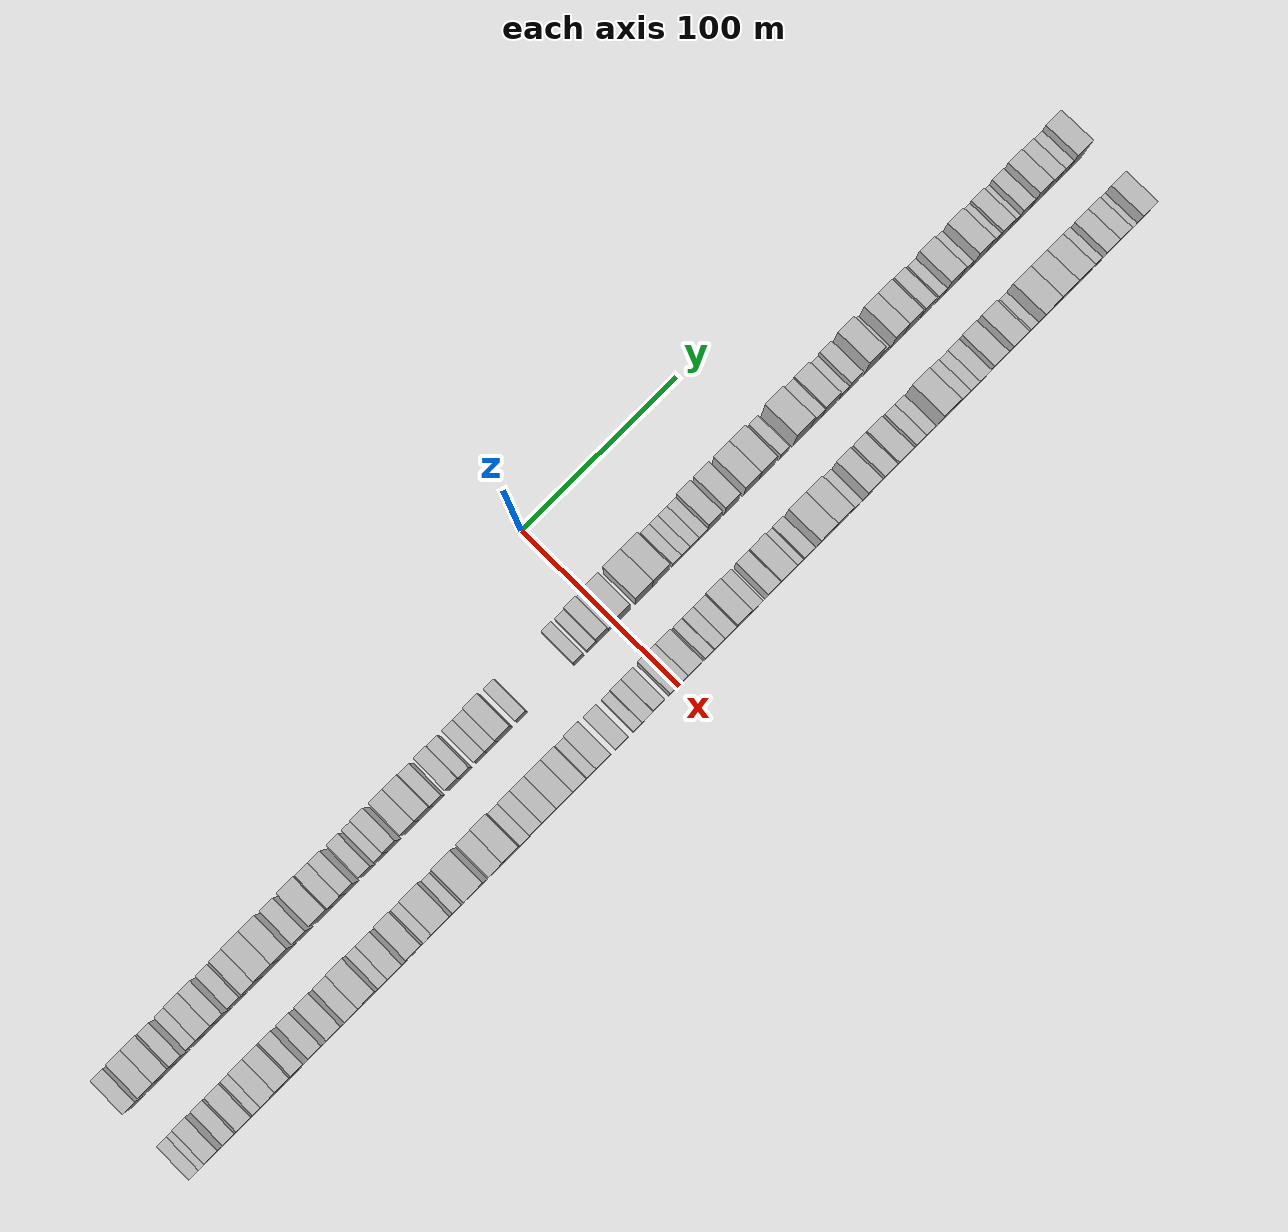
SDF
<sdf version="1.6">
 <world name="default">
  <scene>
   <sky><clouds><speed>12</speed></clouds></sky>
   <ambient>0.4 0.4 0.4 1</ambient>
   <background>0.7 0.7 0.7 1</background>
   <shadows>1</shadows>
  </scene>
  <gravity>0 0 -9.8066</gravity>
  <magnetic_field>6e-06 2.3e-05 -4.2e-05</magnetic_field>
  <physics default="0" name="default_physics" type="ode">
   <ode>
    <solver>
     <type>quick</type>
     <iters>10</iters>
     <sor>1.0</sor>
     <use_dynamic_moi_rescaling>0</use_dynamic_moi_rescaling>
    </solver>
    <constraints>
     <cfm>0</cfm>
     <erp>0.2</erp>
     <contact_max_correcting_vel>100</contact_max_correcting_vel>
     <contact_surface_layer>0.001</contact_surface_layer>
    </constraints>
   </ode>
   <max_step_size>0.004</max_step_size>
   <real_time_factor>1</real_time_factor>
   <real_time_update_rate>250</real_time_update_rate>
  </physics>
  <light name="sun" type="directional">
   <pose>0 0 10 0 0 0</pose>
   <diffuse>0.8 0.8 0.8 1</diffuse>
   <specular>0.2 0.2 0.2 1</specular>
   <attenuation>
    <range>1000</range>
    <constant>0.9</constant>
    <linear>0.01</linear>
    <quadratic>0.001</quadratic>
   </attenuation>
   <direction>-0.5 0.1 -0.9</direction>
  </light>
  <model name="building_1">
   <static>1</static>
   <pose>50.0000 -296.3226 0 0.000000 0.000000 0.000000</pose>
   <link name="link">
    <pose>0 0 7.50 0 0 0</pose>
    <collision name="collision"><geometry><box><size>20.0000 7.3548 15.0000</size></box></geometry></collision>
    <visual name="visual">
     <cast_shadows>0</cast_shadows>
     <geometry><box><size>20.0000 7.3548 15.0000</size></box></geometry>
     <material>
      <script>
       <uri>model://HANNAS_wall/materials/scripts</uri>
       <uri>model://HANNAS_wall/materials/textures</uri>
       <name>vrc/HANNAS_wall</name>
      </script>
     </material>
    </visual>
   </link>
  </model>
  <model name="building_2">
   <static>1</static>
   <pose>50.0000 -285.2588 0 0.000000 0.000000 0.000000</pose>
   <link name="link">
    <pose>0 0 9.00 0 0 0</pose>
    <collision name="collision"><geometry><box><size>20.0000 8.7729 18.0000</size></box></geometry></collision>
    <visual name="visual">
     <cast_shadows>0</cast_shadows>
     <geometry><box><size>20.0000 8.7729 18.0000</size></box></geometry>
     <material>
      <script>
       <uri>model://HANNAS_wall/materials/scripts</uri>
       <uri>model://HANNAS_wall/materials/textures</uri>
       <name>vrc/HANNAS_wall</name>
      </script>
     </material>
    </visual>
   </link>
  </model>
  <model name="building_3">
   <static>1</static>
   <pose>50.0000 -276.5379 0 0.000000 0.000000 0.000000</pose>
   <link name="link">
    <pose>0 0 9.00 0 0 0</pose>
    <collision name="collision"><geometry><box><size>20.0000 8.6689 18.0000</size></box></geometry></collision>
    <visual name="visual">
     <cast_shadows>0</cast_shadows>
     <geometry><box><size>20.0000 8.6689 18.0000</size></box></geometry>
     <material>
      <script>
       <uri>model://HANNAS_wall/materials/scripts</uri>
       <uri>model://HANNAS_wall/materials/textures</uri>
       <name>vrc/HANNAS_wall</name>
      </script>
     </material>
    </visual>
   </link>
  </model>
  <model name="building_4">
   <static>1</static>
   <pose>50.0000 -268.7203 0 0.000000 0.000000 0.000000</pose>
   <link name="link">
    <pose>0 0 7.50 0 0 0</pose>
    <collision name="collision"><geometry><box><size>20.0000 6.9662 15.0000</size></box></geometry></collision>
    <visual name="visual">
     <cast_shadows>0</cast_shadows>
     <geometry><box><size>20.0000 6.9662 15.0000</size></box></geometry>
     <material>
      <script>
       <uri>model://HANNAS_wall/materials/scripts</uri>
       <uri>model://HANNAS_wall/materials/textures</uri>
       <name>vrc/HANNAS_wall</name>
      </script>
     </material>
    </visual>
   </link>
  </model>
  <model name="building_5">
   <static>1</static>
   <pose>50.0000 -258.8322 0 0.000000 0.000000 0.000000</pose>
   <link name="link">
    <pose>0 0 7.50 0 0 0</pose>
    <collision name="collision"><geometry><box><size>20.0000 6.8100 15.0000</size></box></geometry></collision>
    <visual name="visual">
     <cast_shadows>0</cast_shadows>
     <geometry><box><size>20.0000 6.8100 15.0000</size></box></geometry>
     <material>
      <script>
       <uri>model://HANNAS_wall/materials/scripts</uri>
       <uri>model://HANNAS_wall/materials/textures</uri>
       <name>vrc/HANNAS_wall</name>
      </script>
     </material>
    </visual>
   </link>
  </model>
  <model name="building_6">
   <static>1</static>
   <pose>50.0000 -251.1433 0 0.000000 0.000000 0.000000</pose>
   <link name="link">
    <pose>0 0 9.00 0 0 0</pose>
    <collision name="collision"><geometry><box><size>20.0000 8.5678 18.0000</size></box></geometry></collision>
    <visual name="visual">
     <cast_shadows>0</cast_shadows>
     <geometry><box><size>20.0000 8.5678 18.0000</size></box></geometry>
     <material>
      <script>
       <uri>model://HANNAS_wall/materials/scripts</uri>
       <uri>model://HANNAS_wall/materials/textures</uri>
       <name>vrc/HANNAS_wall</name>
      </script>
     </material>
    </visual>
   </link>
  </model>
  <model name="building_7">
   <static>1</static>
   <pose>50.0000 -243.2045 0 0.000000 0.000000 0.000000</pose>
   <link name="link">
    <pose>0 0 9.00 0 0 0</pose>
    <collision name="collision"><geometry><box><size>20.0000 7.3098 18.0000</size></box></geometry></collision>
    <visual name="visual">
     <cast_shadows>0</cast_shadows>
     <geometry><box><size>20.0000 7.3098 18.0000</size></box></geometry>
     <material>
      <script>
       <uri>model://HANNAS_wall/materials/scripts</uri>
       <uri>model://HANNAS_wall/materials/textures</uri>
       <name>vrc/HANNAS_wall</name>
      </script>
     </material>
    </visual>
   </link>
  </model>
  <model name="building_8">
   <static>1</static>
   <pose>50.0000 -233.9707 0 0.000000 0.000000 0.000000</pose>
   <link name="link">
    <pose>0 0 7.50 0 0 0</pose>
    <collision name="collision"><geometry><box><size>20.0000 7.1579 15.0000</size></box></geometry></collision>
    <visual name="visual">
     <cast_shadows>0</cast_shadows>
     <geometry><box><size>20.0000 7.1579 15.0000</size></box></geometry>
     <material>
      <script>
       <uri>model://HANNAS_wall/materials/scripts</uri>
       <uri>model://HANNAS_wall/materials/textures</uri>
       <name>vrc/HANNAS_wall</name>
      </script>
     </material>
    </visual>
   </link>
  </model>
  <model name="building_9">
   <static>1</static>
   <pose>50.0000 -224.2129 0 0.000000 0.000000 0.000000</pose>
   <link name="link">
    <pose>0 0 9.00 0 0 0</pose>
    <collision name="collision"><geometry><box><size>20.0000 8.3578 18.0000</size></box></geometry></collision>
    <visual name="visual">
     <cast_shadows>0</cast_shadows>
     <geometry><box><size>20.0000 8.3578 18.0000</size></box></geometry>
     <material>
      <script>
       <uri>model://HANNAS_wall/materials/scripts</uri>
       <uri>model://HANNAS_wall/materials/textures</uri>
       <name>vrc/HANNAS_wall</name>
      </script>
     </material>
    </visual>
   </link>
  </model>
  <model name="building_10">
   <static>1</static>
   <pose>50.0000 -214.8225 0 0.000000 0.000000 0.000000</pose>
   <link name="link">
    <pose>0 0 10.50 0 0 0</pose>
    <collision name="collision"><geometry><box><size>20.0000 10.4230 21.0000</size></box></geometry></collision>
    <visual name="visual">
     <cast_shadows>0</cast_shadows>
     <geometry><box><size>20.0000 10.4230 21.0000</size></box></geometry>
     <material>
      <script>
       <uri>model://HANNAS_wall/materials/scripts</uri>
       <uri>model://HANNAS_wall/materials/textures</uri>
       <name>vrc/HANNAS_wall</name>
      </script>
     </material>
    </visual>
   </link>
  </model>
  <model name="building_11">
   <static>1</static>
   <pose>50.0000 -204.8685 0 0.000000 0.000000 0.000000</pose>
   <link name="link">
    <pose>0 0 10.50 0 0 0</pose>
    <collision name="collision"><geometry><box><size>20.0000 9.4849 21.0000</size></box></geometry></collision>
    <visual name="visual">
     <cast_shadows>0</cast_shadows>
     <geometry><box><size>20.0000 9.4849 21.0000</size></box></geometry>
     <material>
      <script>
       <uri>model://HANNAS_wall/materials/scripts</uri>
       <uri>model://HANNAS_wall/materials/textures</uri>
       <name>vrc/HANNAS_wall</name>
      </script>
     </material>
    </visual>
   </link>
  </model>
  <model name="building_12">
   <static>1</static>
   <pose>50.0000 -194.1113 0 0.000000 0.000000 0.000000</pose>
   <link name="link">
    <pose>0 0 9.00 0 0 0</pose>
    <collision name="collision"><geometry><box><size>20.0000 8.0295 18.0000</size></box></geometry></collision>
    <visual name="visual">
     <cast_shadows>0</cast_shadows>
     <geometry><box><size>20.0000 8.0295 18.0000</size></box></geometry>
     <material>
      <script>
       <uri>model://HANNAS_wall/materials/scripts</uri>
       <uri>model://HANNAS_wall/materials/textures</uri>
       <name>vrc/HANNAS_wall</name>
      </script>
     </material>
    </visual>
   </link>
  </model>
  <model name="building_13">
   <static>1</static>
   <pose>50.0000 -181.9876 0 0.000000 0.000000 0.000000</pose>
   <link name="link">
    <pose>0 0 10.50 0 0 0</pose>
    <collision name="collision"><geometry><box><size>20.0000 10.2180 21.0000</size></box></geometry></collision>
    <visual name="visual">
     <cast_shadows>0</cast_shadows>
     <geometry><box><size>20.0000 10.2180 21.0000</size></box></geometry>
     <material>
      <script>
       <uri>model://HANNAS_wall/materials/scripts</uri>
       <uri>model://HANNAS_wall/materials/textures</uri>
       <name>vrc/HANNAS_wall</name>
      </script>
     </material>
    </visual>
   </link>
  </model>
  <model name="building_14">
   <static>1</static>
   <pose>50.0000 -172.9549 0 0.000000 0.000000 0.000000</pose>
   <link name="link">
    <pose>0 0 9.00 0 0 0</pose>
    <collision name="collision"><geometry><box><size>20.0000 7.8474 18.0000</size></box></geometry></collision>
    <visual name="visual">
     <cast_shadows>0</cast_shadows>
     <geometry><box><size>20.0000 7.8474 18.0000</size></box></geometry>
     <material>
      <script>
       <uri>model://HANNAS_wall/materials/scripts</uri>
       <uri>model://HANNAS_wall/materials/textures</uri>
       <name>vrc/HANNAS_wall</name>
      </script>
     </material>
    </visual>
   </link>
  </model>
  <model name="building_15">
   <static>1</static>
   <pose>50.0000 -165.3196 0 0.000000 0.000000 0.000000</pose>
   <link name="link">
    <pose>0 0 9.00 0 0 0</pose>
    <collision name="collision"><geometry><box><size>20.0000 7.4234 18.0000</size></box></geometry></collision>
    <visual name="visual">
     <cast_shadows>0</cast_shadows>
     <geometry><box><size>20.0000 7.4234 18.0000</size></box></geometry>
     <material>
      <script>
       <uri>model://HANNAS_wall/materials/scripts</uri>
       <uri>model://HANNAS_wall/materials/textures</uri>
       <name>vrc/HANNAS_wall</name>
      </script>
     </material>
    </visual>
   </link>
  </model>
  <model name="building_16">
   <static>1</static>
   <pose>50.0000 -155.0057 0 0.000000 0.000000 0.000000</pose>
   <link name="link">
    <pose>0 0 7.50 0 0 0</pose>
    <collision name="collision"><geometry><box><size>20.0000 7.2043 15.0000</size></box></geometry></collision>
    <visual name="visual">
     <cast_shadows>0</cast_shadows>
     <geometry><box><size>20.0000 7.2043 15.0000</size></box></geometry>
     <material>
      <script>
       <uri>model://HANNAS_wall/materials/scripts</uri>
       <uri>model://HANNAS_wall/materials/textures</uri>
       <name>vrc/HANNAS_wall</name>
      </script>
     </material>
    </visual>
   </link>
  </model>
  <model name="building_17">
   <static>1</static>
   <pose>50.0000 -146.3915 0 0.000000 0.000000 0.000000</pose>
   <link name="link">
    <pose>0 0 7.50 0 0 0</pose>
    <collision name="collision"><geometry><box><size>20.0000 6.0242 15.0000</size></box></geometry></collision>
    <visual name="visual">
     <cast_shadows>0</cast_shadows>
     <geometry><box><size>20.0000 6.0242 15.0000</size></box></geometry>
     <material>
      <script>
       <uri>model://HANNAS_wall/materials/scripts</uri>
       <uri>model://HANNAS_wall/materials/textures</uri>
       <name>vrc/HANNAS_wall</name>
      </script>
     </material>
    </visual>
   </link>
  </model>
  <model name="building_18">
   <static>1</static>
   <pose>50.0000 -139.5196 0 0.000000 0.000000 0.000000</pose>
   <link name="link">
    <pose>0 0 9.00 0 0 0</pose>
    <collision name="collision"><geometry><box><size>20.0000 7.7195 18.0000</size></box></geometry></collision>
    <visual name="visual">
     <cast_shadows>0</cast_shadows>
     <geometry><box><size>20.0000 7.7195 18.0000</size></box></geometry>
     <material>
      <script>
       <uri>model://HANNAS_wall/materials/scripts</uri>
       <uri>model://HANNAS_wall/materials/textures</uri>
       <name>vrc/HANNAS_wall</name>
      </script>
     </material>
    </visual>
   </link>
  </model>
  <model name="building_19">
   <static>1</static>
   <pose>50.0000 -128.3467 0 0.000000 0.000000 0.000000</pose>
   <link name="link">
    <pose>0 0 9.00 0 0 0</pose>
    <collision name="collision"><geometry><box><size>20.0000 8.6264 18.0000</size></box></geometry></collision>
    <visual name="visual">
     <cast_shadows>0</cast_shadows>
     <geometry><box><size>20.0000 8.6264 18.0000</size></box></geometry>
     <material>
      <script>
       <uri>model://HANNAS_wall/materials/scripts</uri>
       <uri>model://HANNAS_wall/materials/textures</uri>
       <name>vrc/HANNAS_wall</name>
      </script>
     </material>
    </visual>
   </link>
  </model>
  <model name="building_20">
   <static>1</static>
   <pose>50.0000 -119.6518 0 0.000000 0.000000 0.000000</pose>
   <link name="link">
    <pose>0 0 9.00 0 0 0</pose>
    <collision name="collision"><geometry><box><size>20.0000 8.7634 18.0000</size></box></geometry></collision>
    <visual name="visual">
     <cast_shadows>0</cast_shadows>
     <geometry><box><size>20.0000 8.7634 18.0000</size></box></geometry>
     <material>
      <script>
       <uri>model://HANNAS_wall/materials/scripts</uri>
       <uri>model://HANNAS_wall/materials/textures</uri>
       <name>vrc/HANNAS_wall</name>
      </script>
     </material>
    </visual>
   </link>
  </model>
  <model name="building_21">
   <static>1</static>
   <pose>50.0000 -111.7621 0 0.000000 0.000000 0.000000</pose>
   <link name="link">
    <pose>0 0 7.50 0 0 0</pose>
    <collision name="collision"><geometry><box><size>20.0000 7.0159 15.0000</size></box></geometry></collision>
    <visual name="visual">
     <cast_shadows>0</cast_shadows>
     <geometry><box><size>20.0000 7.0159 15.0000</size></box></geometry>
     <material>
      <script>
       <uri>model://HANNAS_wall/materials/scripts</uri>
       <uri>model://HANNAS_wall/materials/textures</uri>
       <name>vrc/HANNAS_wall</name>
      </script>
     </material>
    </visual>
   </link>
  </model>
  <model name="building_22">
   <static>1</static>
   <pose>50.0000 -101.4349 0 0.000000 0.000000 0.000000</pose>
   <link name="link">
    <pose>0 0 9.00 0 0 0</pose>
    <collision name="collision"><geometry><box><size>20.0000 7.6385 18.0000</size></box></geometry></collision>
    <visual name="visual">
     <cast_shadows>0</cast_shadows>
     <geometry><box><size>20.0000 7.6385 18.0000</size></box></geometry>
     <material>
      <script>
       <uri>model://HANNAS_wall/materials/scripts</uri>
       <uri>model://HANNAS_wall/materials/textures</uri>
       <name>vrc/HANNAS_wall</name>
      </script>
     </material>
    </visual>
   </link>
  </model>
  <model name="building_23">
   <static>1</static>
   <pose>50.0000 -94.3597 0 0.000000 0.000000 0.000000</pose>
   <link name="link">
    <pose>0 0 7.50 0 0 0</pose>
    <collision name="collision"><geometry><box><size>20.0000 6.5120 15.0000</size></box></geometry></collision>
    <visual name="visual">
     <cast_shadows>0</cast_shadows>
     <geometry><box><size>20.0000 6.5120 15.0000</size></box></geometry>
     <material>
      <script>
       <uri>model://HANNAS_wall/materials/scripts</uri>
       <uri>model://HANNAS_wall/materials/textures</uri>
       <name>vrc/HANNAS_wall</name>
      </script>
     </material>
    </visual>
   </link>
  </model>
  <model name="building_24">
   <static>1</static>
   <pose>50.0000 -84.7293 0 0.000000 0.000000 0.000000</pose>
   <link name="link">
    <pose>0 0 7.50 0 0 0</pose>
    <collision name="collision"><geometry><box><size>20.0000 6.7488 15.0000</size></box></geometry></collision>
    <visual name="visual">
     <cast_shadows>0</cast_shadows>
     <geometry><box><size>20.0000 6.7488 15.0000</size></box></geometry>
     <material>
      <script>
       <uri>model://HANNAS_wall/materials/scripts</uri>
       <uri>model://HANNAS_wall/materials/textures</uri>
       <name>vrc/HANNAS_wall</name>
      </script>
     </material>
    </visual>
   </link>
  </model>
  <model name="building_25">
   <static>1</static>
   <pose>50.0000 -78.0399 0 0.000000 0.000000 0.000000</pose>
   <link name="link">
    <pose>0 0 7.50 0 0 0</pose>
    <collision name="collision"><geometry><box><size>20.0000 6.6301 15.0000</size></box></geometry></collision>
    <visual name="visual">
     <cast_shadows>0</cast_shadows>
     <geometry><box><size>20.0000 6.6301 15.0000</size></box></geometry>
     <material>
      <script>
       <uri>model://HANNAS_wall/materials/scripts</uri>
       <uri>model://HANNAS_wall/materials/textures</uri>
       <name>vrc/HANNAS_wall</name>
      </script>
     </material>
    </visual>
   </link>
  </model>
  <model name="building_26">
   <static>1</static>
   <pose>50.0000 -70.1083 0 0.000000 0.000000 0.000000</pose>
   <link name="link">
    <pose>0 0 10.50 0 0 0</pose>
    <collision name="collision"><geometry><box><size>20.0000 9.2331 21.0000</size></box></geometry></collision>
    <visual name="visual">
     <cast_shadows>0</cast_shadows>
     <geometry><box><size>20.0000 9.2331 21.0000</size></box></geometry>
     <material>
      <script>
       <uri>model://HANNAS_wall/materials/scripts</uri>
       <uri>model://HANNAS_wall/materials/textures</uri>
       <name>vrc/HANNAS_wall</name>
      </script>
     </material>
    </visual>
   </link>
  </model>
  <model name="building_27">
   <static>1</static>
   <pose>50.0000 -59.2978 0 0.000000 0.000000 0.000000</pose>
   <link name="link">
    <pose>0 0 7.50 0 0 0</pose>
    <collision name="collision"><geometry><box><size>20.0000 6.3880 15.0000</size></box></geometry></collision>
    <visual name="visual">
     <cast_shadows>0</cast_shadows>
     <geometry><box><size>20.0000 6.3880 15.0000</size></box></geometry>
     <material>
      <script>
       <uri>model://HANNAS_wall/materials/scripts</uri>
       <uri>model://HANNAS_wall/materials/textures</uri>
       <name>vrc/HANNAS_wall</name>
      </script>
     </material>
    </visual>
   </link>
  </model>
  <model name="building_28">
   <static>1</static>
   <pose>50.0000 -23.5410 0 0.000000 0.000000 0.000000</pose>
   <link name="link">
    <pose>0 0 7.50 0 0 0</pose>
    <collision name="collision"><geometry><box><size>20.0000 6.3752 15.0000</size></box></geometry></collision>
    <visual name="visual">
     <cast_shadows>0</cast_shadows>
     <geometry><box><size>20.0000 6.3752 15.0000</size></box></geometry>
     <material>
      <script>
       <uri>model://HANNAS_wall/materials/scripts</uri>
       <uri>model://HANNAS_wall/materials/textures</uri>
       <name>vrc/HANNAS_wall</name>
      </script>
     </material>
    </visual>
   </link>
  </model>
  <model name="building_29">
   <static>1</static>
   <pose>50.0000 -15.4080 0 0.000000 0.000000 0.000000</pose>
   <link name="link">
    <pose>0 0 6.00 0 0 0</pose>
    <collision name="collision"><geometry><box><size>20.0000 5.8906 12.0000</size></box></geometry></collision>
    <visual name="visual">
     <cast_shadows>0</cast_shadows>
     <geometry><box><size>20.0000 5.8906 12.0000</size></box></geometry>
     <material>
      <script>
       <uri>model://HANNAS_wall/materials/scripts</uri>
       <uri>model://HANNAS_wall/materials/textures</uri>
       <name>vrc/HANNAS_wall</name>
      </script>
     </material>
    </visual>
   </link>
  </model>
  <model name="building_30">
   <static>1</static>
   <pose>50.0000 -8.6986 0 0.000000 0.000000 0.000000</pose>
   <link name="link">
    <pose>0 0 9.00 0 0 0</pose>
    <collision name="collision"><geometry><box><size>20.0000 7.5284 18.0000</size></box></geometry></collision>
    <visual name="visual">
     <cast_shadows>0</cast_shadows>
     <geometry><box><size>20.0000 7.5284 18.0000</size></box></geometry>
     <material>
      <script>
       <uri>model://HANNAS_wall/materials/scripts</uri>
       <uri>model://HANNAS_wall/materials/textures</uri>
       <name>vrc/HANNAS_wall</name>
      </script>
     </material>
    </visual>
   </link>
  </model>
  <model name="building_31">
   <static>1</static>
   <pose>50.0000 -2.3356 0 0.000000 0.000000 0.000000</pose>
   <link name="link">
    <pose>0 0 6.00 0 0 0</pose>
    <collision name="collision"><geometry><box><size>20.0000 5.1975 12.0000</size></box></geometry></collision>
    <visual name="visual">
     <cast_shadows>0</cast_shadows>
     <geometry><box><size>20.0000 5.1975 12.0000</size></box></geometry>
     <material>
      <script>
       <uri>model://HANNAS_wall/materials/scripts</uri>
       <uri>model://HANNAS_wall/materials/textures</uri>
       <name>vrc/HANNAS_wall</name>
      </script>
     </material>
    </visual>
   </link>
  </model>
  <model name="building_32">
   <static>1</static>
   <pose>50.0000 4.6970 0 0.000000 0.000000 0.000000</pose>
   <link name="link">
    <pose>0 0 10.50 0 0 0</pose>
    <collision name="collision"><geometry><box><size>20.0000 8.8677 21.0000</size></box></geometry></collision>
    <visual name="visual">
     <cast_shadows>0</cast_shadows>
     <geometry><box><size>20.0000 8.8677 21.0000</size></box></geometry>
     <material>
      <script>
       <uri>model://HANNAS_wall/materials/scripts</uri>
       <uri>model://HANNAS_wall/materials/textures</uri>
       <name>vrc/HANNAS_wall</name>
      </script>
     </material>
    </visual>
   </link>
  </model>
  <model name="building_33">
   <static>1</static>
   <pose>50.0000 17.7263 0 0.000000 0.000000 0.000000</pose>
   <link name="link">
    <pose>0 0 12.00 0 0 0</pose>
    <collision name="collision"><geometry><box><size>20.0000 11.1909 24.0000</size></box></geometry></collision>
    <visual name="visual">
     <cast_shadows>0</cast_shadows>
     <geometry><box><size>20.0000 11.1909 24.0000</size></box></geometry>
     <material>
      <script>
       <uri>model://HANNAS_wall/materials/scripts</uri>
       <uri>model://HANNAS_wall/materials/textures</uri>
       <name>vrc/HANNAS_wall</name>
      </script>
     </material>
    </visual>
   </link>
  </model>
  <model name="building_34">
   <static>1</static>
   <pose>50.0000 28.5475 0 0.000000 0.000000 0.000000</pose>
   <link name="link">
    <pose>0 0 12.00 0 0 0</pose>
    <collision name="collision"><geometry><box><size>20.0000 10.4515 24.0000</size></box></geometry></collision>
    <visual name="visual">
     <cast_shadows>0</cast_shadows>
     <geometry><box><size>20.0000 10.4515 24.0000</size></box></geometry>
     <material>
      <script>
       <uri>model://HANNAS_wall/materials/scripts</uri>
       <uri>model://HANNAS_wall/materials/textures</uri>
       <name>vrc/HANNAS_wall</name>
      </script>
     </material>
    </visual>
   </link>
  </model>
  <model name="building_35">
   <static>1</static>
   <pose>50.0000 38.5941 0 0.000000 0.000000 0.000000</pose>
   <link name="link">
    <pose>0 0 6.00 0 0 0</pose>
    <collision name="collision"><geometry><box><size>20.0000 5.6416 12.0000</size></box></geometry></collision>
    <visual name="visual">
     <cast_shadows>0</cast_shadows>
     <geometry><box><size>20.0000 5.6416 12.0000</size></box></geometry>
     <material>
      <script>
       <uri>model://HANNAS_wall/materials/scripts</uri>
       <uri>model://HANNAS_wall/materials/textures</uri>
       <name>vrc/HANNAS_wall</name>
      </script>
     </material>
    </visual>
   </link>
  </model>
  <model name="building_36">
   <static>1</static>
   <pose>50.0000 44.1248 0 0.000000 0.000000 0.000000</pose>
   <link name="link">
    <pose>0 0 6.00 0 0 0</pose>
    <collision name="collision"><geometry><box><size>20.0000 5.4198 12.0000</size></box></geometry></collision>
    <visual name="visual">
     <cast_shadows>0</cast_shadows>
     <geometry><box><size>20.0000 5.4198 12.0000</size></box></geometry>
     <material>
      <script>
       <uri>model://HANNAS_wall/materials/scripts</uri>
       <uri>model://HANNAS_wall/materials/textures</uri>
       <name>vrc/HANNAS_wall</name>
      </script>
     </material>
    </visual>
   </link>
  </model>
  <model name="building_37">
   <static>1</static>
   <pose>50.0000 49.7424 0 0.000000 0.000000 0.000000</pose>
   <link name="link">
    <pose>0 0 6.00 0 0 0</pose>
    <collision name="collision"><geometry><box><size>20.0000 5.8154 12.0000</size></box></geometry></collision>
    <visual name="visual">
     <cast_shadows>0</cast_shadows>
     <geometry><box><size>20.0000 5.8154 12.0000</size></box></geometry>
     <material>
      <script>
       <uri>model://HANNAS_wall/materials/scripts</uri>
       <uri>model://HANNAS_wall/materials/textures</uri>
       <name>vrc/HANNAS_wall</name>
      </script>
     </material>
    </visual>
   </link>
  </model>
  <model name="building_38">
   <static>1</static>
   <pose>50.0000 55.4528 0 0.000000 0.000000 0.000000</pose>
   <link name="link">
    <pose>0 0 6.00 0 0 0</pose>
    <collision name="collision"><geometry><box><size>20.0000 5.6054 12.0000</size></box></geometry></collision>
    <visual name="visual">
     <cast_shadows>0</cast_shadows>
     <geometry><box><size>20.0000 5.6054 12.0000</size></box></geometry>
     <material>
      <script>
       <uri>model://HANNAS_wall/materials/scripts</uri>
       <uri>model://HANNAS_wall/materials/textures</uri>
       <name>vrc/HANNAS_wall</name>
      </script>
     </material>
    </visual>
   </link>
  </model>
  <model name="building_39">
   <static>1</static>
   <pose>50.0000 62.6097 0 0.000000 0.000000 0.000000</pose>
   <link name="link">
    <pose>0 0 10.50 0 0 0</pose>
    <collision name="collision"><geometry><box><size>20.0000 8.7083 21.0000</size></box></geometry></collision>
    <visual name="visual">
     <cast_shadows>0</cast_shadows>
     <geometry><box><size>20.0000 8.7083 21.0000</size></box></geometry>
     <material>
      <script>
       <uri>model://HANNAS_wall/materials/scripts</uri>
       <uri>model://HANNAS_wall/materials/textures</uri>
       <name>vrc/HANNAS_wall</name>
      </script>
     </material>
    </visual>
   </link>
  </model>
  <model name="building_40">
   <static>1</static>
   <pose>50.0000 73.7366 0 0.000000 0.000000 0.000000</pose>
   <link name="link">
    <pose>0 0 10.50 0 0 0</pose>
    <collision name="collision"><geometry><box><size>20.0000 9.5457 21.0000</size></box></geometry></collision>
    <visual name="visual">
     <cast_shadows>0</cast_shadows>
     <geometry><box><size>20.0000 9.5457 21.0000</size></box></geometry>
     <material>
      <script>
       <uri>model://HANNAS_wall/materials/scripts</uri>
       <uri>model://HANNAS_wall/materials/textures</uri>
       <name>vrc/HANNAS_wall</name>
      </script>
     </material>
    </visual>
   </link>
  </model>
  <model name="building_41">
   <static>1</static>
   <pose>50.0000 86.5715 0 0.000000 0.000000 0.000000</pose>
   <link name="link">
    <pose>0 0 10.50 0 0 0</pose>
    <collision name="collision"><geometry><box><size>20.0000 10.1241 21.0000</size></box></geometry></collision>
    <visual name="visual">
     <cast_shadows>0</cast_shadows>
     <geometry><box><size>20.0000 10.1241 21.0000</size></box></geometry>
     <material>
      <script>
       <uri>model://HANNAS_wall/materials/scripts</uri>
       <uri>model://HANNAS_wall/materials/textures</uri>
       <name>vrc/HANNAS_wall</name>
      </script>
     </material>
    </visual>
   </link>
  </model>
  <model name="building_42">
   <static>1</static>
   <pose>50.0000 96.6998 0 0.000000 0.000000 0.000000</pose>
   <link name="link">
    <pose>0 0 10.50 0 0 0</pose>
    <collision name="collision"><geometry><box><size>20.0000 10.1325 21.0000</size></box></geometry></collision>
    <visual name="visual">
     <cast_shadows>0</cast_shadows>
     <geometry><box><size>20.0000 10.1325 21.0000</size></box></geometry>
     <material>
      <script>
       <uri>model://HANNAS_wall/materials/scripts</uri>
       <uri>model://HANNAS_wall/materials/textures</uri>
       <name>vrc/HANNAS_wall</name>
      </script>
     </material>
    </visual>
   </link>
  </model>
  <model name="building_43">
   <static>1</static>
   <pose>50.0000 107.6959 0 0.000000 0.000000 0.000000</pose>
   <link name="link">
    <pose>0 0 6.00 0 0 0</pose>
    <collision name="collision"><geometry><box><size>20.0000 5.8596 12.0000</size></box></geometry></collision>
    <visual name="visual">
     <cast_shadows>0</cast_shadows>
     <geometry><box><size>20.0000 5.8596 12.0000</size></box></geometry>
     <material>
      <script>
       <uri>model://HANNAS_wall/materials/scripts</uri>
       <uri>model://HANNAS_wall/materials/textures</uri>
       <name>vrc/HANNAS_wall</name>
      </script>
     </material>
    </visual>
   </link>
  </model>
  <model name="building_44">
   <static>1</static>
   <pose>50.0000 119.4271 0 0.000000 0.000000 0.000000</pose>
   <link name="link">
    <pose>0 0 12.00 0 0 0</pose>
    <collision name="collision"><geometry><box><size>20.0000 11.6029 24.0000</size></box></geometry></collision>
    <visual name="visual">
     <cast_shadows>0</cast_shadows>
     <geometry><box><size>20.0000 11.6029 24.0000</size></box></geometry>
     <material>
      <script>
       <uri>model://HANNAS_wall/materials/scripts</uri>
       <uri>model://HANNAS_wall/materials/textures</uri>
       <name>vrc/HANNAS_wall</name>
      </script>
     </material>
    </visual>
   </link>
  </model>
  <model name="building_45">
   <static>1</static>
   <pose>50.0000 128.8334 0 0.000000 0.000000 0.000000</pose>
   <link name="link">
    <pose>0 0 9.00 0 0 0</pose>
    <collision name="collision"><geometry><box><size>20.0000 7.2097 18.0000</size></box></geometry></collision>
    <visual name="visual">
     <cast_shadows>0</cast_shadows>
     <geometry><box><size>20.0000 7.2097 18.0000</size></box></geometry>
     <material>
      <script>
       <uri>model://HANNAS_wall/materials/scripts</uri>
       <uri>model://HANNAS_wall/materials/textures</uri>
       <name>vrc/HANNAS_wall</name>
      </script>
     </material>
    </visual>
   </link>
  </model>
  <model name="building_46">
   <static>1</static>
   <pose>50.0000 137.2449 0 0.000000 0.000000 0.000000</pose>
   <link name="link">
    <pose>0 0 10.50 0 0 0</pose>
    <collision name="collision"><geometry><box><size>20.0000 9.6132 21.0000</size></box></geometry></collision>
    <visual name="visual">
     <cast_shadows>0</cast_shadows>
     <geometry><box><size>20.0000 9.6132 21.0000</size></box></geometry>
     <material>
      <script>
       <uri>model://HANNAS_wall/materials/scripts</uri>
       <uri>model://HANNAS_wall/materials/textures</uri>
       <name>vrc/HANNAS_wall</name>
      </script>
     </material>
    </visual>
   </link>
  </model>
  <model name="building_47">
   <static>1</static>
   <pose>50.0000 146.5367 0 0.000000 0.000000 0.000000</pose>
   <link name="link">
    <pose>0 0 6.00 0 0 0</pose>
    <collision name="collision"><geometry><box><size>20.0000 4.9704 12.0000</size></box></geometry></collision>
    <visual name="visual">
     <cast_shadows>0</cast_shadows>
     <geometry><box><size>20.0000 4.9704 12.0000</size></box></geometry>
     <material>
      <script>
       <uri>model://HANNAS_wall/materials/scripts</uri>
       <uri>model://HANNAS_wall/materials/textures</uri>
       <name>vrc/HANNAS_wall</name>
      </script>
     </material>
    </visual>
   </link>
  </model>
  <model name="building_48">
   <static>1</static>
   <pose>50.0000 152.8156 0 0.000000 0.000000 0.000000</pose>
   <link name="link">
    <pose>0 0 9.00 0 0 0</pose>
    <collision name="collision"><geometry><box><size>20.0000 7.5873 18.0000</size></box></geometry></collision>
    <visual name="visual">
     <cast_shadows>0</cast_shadows>
     <geometry><box><size>20.0000 7.5873 18.0000</size></box></geometry>
     <material>
      <script>
       <uri>model://HANNAS_wall/materials/scripts</uri>
       <uri>model://HANNAS_wall/materials/textures</uri>
       <name>vrc/HANNAS_wall</name>
      </script>
     </material>
    </visual>
   </link>
  </model>
  <model name="building_49">
   <static>1</static>
   <pose>50.0000 164.7333 0 0.000000 0.000000 0.000000</pose>
   <link name="link">
    <pose>0 0 12.00 0 0 0</pose>
    <collision name="collision"><geometry><box><size>20.0000 10.2480 24.0000</size></box></geometry></collision>
    <visual name="visual">
     <cast_shadows>0</cast_shadows>
     <geometry><box><size>20.0000 10.2480 24.0000</size></box></geometry>
     <material>
      <script>
       <uri>model://HANNAS_wall/materials/scripts</uri>
       <uri>model://HANNAS_wall/materials/textures</uri>
       <name>vrc/HANNAS_wall</name>
      </script>
     </material>
    </visual>
   </link>
  </model>
  <model name="building_50">
   <static>1</static>
   <pose>50.0000 172.4840 0 0.000000 0.000000 0.000000</pose>
   <link name="link">
    <pose>0 0 6.00 0 0 0</pose>
    <collision name="collision"><geometry><box><size>20.0000 5.2534 12.0000</size></box></geometry></collision>
    <visual name="visual">
     <cast_shadows>0</cast_shadows>
     <geometry><box><size>20.0000 5.2534 12.0000</size></box></geometry>
     <material>
      <script>
       <uri>model://HANNAS_wall/materials/scripts</uri>
       <uri>model://HANNAS_wall/materials/textures</uri>
       <name>vrc/HANNAS_wall</name>
      </script>
     </material>
    </visual>
   </link>
  </model>
  <model name="building_51">
   <static>1</static>
   <pose>50.0000 181.5382 0 0.000000 0.000000 0.000000</pose>
   <link name="link">
    <pose>0 0 10.50 0 0 0</pose>
    <collision name="collision"><geometry><box><size>20.0000 8.8549 21.0000</size></box></geometry></collision>
    <visual name="visual">
     <cast_shadows>0</cast_shadows>
     <geometry><box><size>20.0000 8.8549 21.0000</size></box></geometry>
     <material>
      <script>
       <uri>model://HANNAS_wall/materials/scripts</uri>
       <uri>model://HANNAS_wall/materials/textures</uri>
       <name>vrc/HANNAS_wall</name>
      </script>
     </material>
    </visual>
   </link>
  </model>
  <model name="building_52">
   <static>1</static>
   <pose>50.0000 190.4332 0 0.000000 0.000000 0.000000</pose>
   <link name="link">
    <pose>0 0 10.50 0 0 0</pose>
    <collision name="collision"><geometry><box><size>20.0000 8.9350 21.0000</size></box></geometry></collision>
    <visual name="visual">
     <cast_shadows>0</cast_shadows>
     <geometry><box><size>20.0000 8.9350 21.0000</size></box></geometry>
     <material>
      <script>
       <uri>model://HANNAS_wall/materials/scripts</uri>
       <uri>model://HANNAS_wall/materials/textures</uri>
       <name>vrc/HANNAS_wall</name>
      </script>
     </material>
    </visual>
   </link>
  </model>
  <model name="building_53">
   <static>1</static>
   <pose>50.0000 200.5397 0 0.000000 0.000000 0.000000</pose>
   <link name="link">
    <pose>0 0 9.00 0 0 0</pose>
    <collision name="collision"><geometry><box><size>20.0000 7.2780 18.0000</size></box></geometry></collision>
    <visual name="visual">
     <cast_shadows>0</cast_shadows>
     <geometry><box><size>20.0000 7.2780 18.0000</size></box></geometry>
     <material>
      <script>
       <uri>model://HANNAS_wall/materials/scripts</uri>
       <uri>model://HANNAS_wall/materials/textures</uri>
       <name>vrc/HANNAS_wall</name>
      </script>
     </material>
    </visual>
   </link>
  </model>
  <model name="building_54">
   <static>1</static>
   <pose>50.0000 209.8873 0 0.000000 0.000000 0.000000</pose>
   <link name="link">
    <pose>0 0 6.00 0 0 0</pose>
    <collision name="collision"><geometry><box><size>20.0000 5.4173 12.0000</size></box></geometry></collision>
    <visual name="visual">
     <cast_shadows>0</cast_shadows>
     <geometry><box><size>20.0000 5.4173 12.0000</size></box></geometry>
     <material>
      <script>
       <uri>model://HANNAS_wall/materials/scripts</uri>
       <uri>model://HANNAS_wall/materials/textures</uri>
       <name>vrc/HANNAS_wall</name>
      </script>
     </material>
    </visual>
   </link>
  </model>
  <model name="building_55">
   <static>1</static>
   <pose>50.0000 217.5736 0 0.000000 0.000000 0.000000</pose>
   <link name="link">
    <pose>0 0 10.50 0 0 0</pose>
    <collision name="collision"><geometry><box><size>20.0000 9.9553 21.0000</size></box></geometry></collision>
    <visual name="visual">
     <cast_shadows>0</cast_shadows>
     <geometry><box><size>20.0000 9.9553 21.0000</size></box></geometry>
     <material>
      <script>
       <uri>model://HANNAS_wall/materials/scripts</uri>
       <uri>model://HANNAS_wall/materials/textures</uri>
       <name>vrc/HANNAS_wall</name>
      </script>
     </material>
    </visual>
   </link>
  </model>
  <model name="building_56">
   <static>1</static>
   <pose>50.0000 225.7262 0 0.000000 0.000000 0.000000</pose>
   <link name="link">
    <pose>0 0 7.50 0 0 0</pose>
    <collision name="collision"><geometry><box><size>20.0000 6.3499 15.0000</size></box></geometry></collision>
    <visual name="visual">
     <cast_shadows>0</cast_shadows>
     <geometry><box><size>20.0000 6.3499 15.0000</size></box></geometry>
     <material>
      <script>
       <uri>model://HANNAS_wall/materials/scripts</uri>
       <uri>model://HANNAS_wall/materials/textures</uri>
       <name>vrc/HANNAS_wall</name>
      </script>
     </material>
    </visual>
   </link>
  </model>
  <model name="building_57">
   <static>1</static>
   <pose>50.0000 235.9621 0 0.000000 0.000000 0.000000</pose>
   <link name="link">
    <pose>0 0 10.50 0 0 0</pose>
    <collision name="collision"><geometry><box><size>20.0000 10.1217 21.0000</size></box></geometry></collision>
    <visual name="visual">
     <cast_shadows>0</cast_shadows>
     <geometry><box><size>20.0000 10.1217 21.0000</size></box></geometry>
     <material>
      <script>
       <uri>model://HANNAS_wall/materials/scripts</uri>
       <uri>model://HANNAS_wall/materials/textures</uri>
       <name>vrc/HANNAS_wall</name>
      </script>
     </material>
    </visual>
   </link>
  </model>
  <model name="building_58">
   <static>1</static>
   <pose>50.0000 244.0430 0 0.000000 0.000000 0.000000</pose>
   <link name="link">
    <pose>0 0 7.50 0 0 0</pose>
    <collision name="collision"><geometry><box><size>20.0000 6.0402 15.0000</size></box></geometry></collision>
    <visual name="visual">
     <cast_shadows>0</cast_shadows>
     <geometry><box><size>20.0000 6.0402 15.0000</size></box></geometry>
     <material>
      <script>
       <uri>model://HANNAS_wall/materials/scripts</uri>
       <uri>model://HANNAS_wall/materials/textures</uri>
       <name>vrc/HANNAS_wall</name>
      </script>
     </material>
    </visual>
   </link>
  </model>
  <model name="building_59">
   <static>1</static>
   <pose>50.0000 251.2206 0 0.000000 0.000000 0.000000</pose>
   <link name="link">
    <pose>0 0 9.00 0 0 0</pose>
    <collision name="collision"><geometry><box><size>20.0000 8.3151 18.0000</size></box></geometry></collision>
    <visual name="visual">
     <cast_shadows>0</cast_shadows>
     <geometry><box><size>20.0000 8.3151 18.0000</size></box></geometry>
     <material>
      <script>
       <uri>model://HANNAS_wall/materials/scripts</uri>
       <uri>model://HANNAS_wall/materials/textures</uri>
       <name>vrc/HANNAS_wall</name>
      </script>
     </material>
    </visual>
   </link>
  </model>
  <model name="building_60">
   <static>1</static>
   <pose>50.0000 258.0000 0 0.000000 0.000000 0.000000</pose>
   <link name="link">
    <pose>0 0 6.00 0 0 0</pose>
    <collision name="collision"><geometry><box><size>20.0000 5.2437 12.0000</size></box></geometry></collision>
    <visual name="visual">
     <cast_shadows>0</cast_shadows>
     <geometry><box><size>20.0000 5.2437 12.0000</size></box></geometry>
     <material>
      <script>
       <uri>model://HANNAS_wall/materials/scripts</uri>
       <uri>model://HANNAS_wall/materials/textures</uri>
       <name>vrc/HANNAS_wall</name>
      </script>
     </material>
    </visual>
   </link>
  </model>
  <model name="building_61">
   <static>1</static>
   <pose>50.0000 264.3909 0 0.000000 0.000000 0.000000</pose>
   <link name="link">
    <pose>0 0 9.00 0 0 0</pose>
    <collision name="collision"><geometry><box><size>20.0000 7.5382 18.0000</size></box></geometry></collision>
    <visual name="visual">
     <cast_shadows>0</cast_shadows>
     <geometry><box><size>20.0000 7.5382 18.0000</size></box></geometry>
     <material>
      <script>
       <uri>model://HANNAS_wall/materials/scripts</uri>
       <uri>model://HANNAS_wall/materials/textures</uri>
       <name>vrc/HANNAS_wall</name>
      </script>
     </material>
    </visual>
   </link>
  </model>
  <model name="building_62">
   <static>1</static>
   <pose>50.0000 274.6211 0 0.000000 0.000000 0.000000</pose>
   <link name="link">
    <pose>0 0 10.50 0 0 0</pose>
    <collision name="collision"><geometry><box><size>20.0000 8.9221 21.0000</size></box></geometry></collision>
    <visual name="visual">
     <cast_shadows>0</cast_shadows>
     <geometry><box><size>20.0000 8.9221 21.0000</size></box></geometry>
     <material>
      <script>
       <uri>model://HANNAS_wall/materials/scripts</uri>
       <uri>model://HANNAS_wall/materials/textures</uri>
       <name>vrc/HANNAS_wall</name>
      </script>
     </material>
    </visual>
   </link>
  </model>
  <model name="building_63">
   <static>1</static>
   <pose>50.0000 283.4762 0 0.000000 0.000000 0.000000</pose>
   <link name="link">
    <pose>0 0 9.00 0 0 0</pose>
    <collision name="collision"><geometry><box><size>20.0000 8.7880 18.0000</size></box></geometry></collision>
    <visual name="visual">
     <cast_shadows>0</cast_shadows>
     <geometry><box><size>20.0000 8.7880 18.0000</size></box></geometry>
     <material>
      <script>
       <uri>model://HANNAS_wall/materials/scripts</uri>
       <uri>model://HANNAS_wall/materials/textures</uri>
       <name>vrc/HANNAS_wall</name>
      </script>
     </material>
    </visual>
   </link>
  </model>
  <model name="building_64">
   <static>1</static>
   <pose>50.0000 291.2876 0 0.000000 0.000000 0.000000</pose>
   <link name="link">
    <pose>0 0 7.50 0 0 0</pose>
    <collision name="collision"><geometry><box><size>20.0000 6.8347 15.0000</size></box></geometry></collision>
    <visual name="visual">
     <cast_shadows>0</cast_shadows>
     <geometry><box><size>20.0000 6.8347 15.0000</size></box></geometry>
     <material>
      <script>
       <uri>model://HANNAS_wall/materials/scripts</uri>
       <uri>model://HANNAS_wall/materials/textures</uri>
       <name>vrc/HANNAS_wall</name>
      </script>
     </material>
    </visual>
   </link>
  </model>
  <model name="building_65">
   <static>1</static>
   <pose>50.0000 299.7510 0 0.000000 0.000000 0.000000</pose>
   <link name="link">
    <pose>0 0 10.50 0 0 0</pose>
    <collision name="collision"><geometry><box><size>20.0000 10.0922 21.0000</size></box></geometry></collision>
    <visual name="visual">
     <cast_shadows>0</cast_shadows>
     <geometry><box><size>20.0000 10.0922 21.0000</size></box></geometry>
     <material>
      <script>
       <uri>model://HANNAS_wall/materials/scripts</uri>
       <uri>model://HANNAS_wall/materials/textures</uri>
       <name>vrc/HANNAS_wall</name>
      </script>
     </material>
    </visual>
   </link>
  </model>
  <model name="building_66">
   <static>1</static>
   <pose>90.0000 -297.0856 0 0.000000 0.000000 0.000000</pose>
   <link name="link">
    <pose>0 0 6.00 0 0 0</pose>
    <collision name="collision"><geometry><box><size>20.0000 5.8288 12.0000</size></box></geometry></collision>
    <visual name="visual">
     <cast_shadows>0</cast_shadows>
     <geometry><box><size>20.0000 5.8288 12.0000</size></box></geometry>
     <material>
      <script>
       <uri>model://HANNAS_wall/materials/scripts</uri>
       <uri>model://HANNAS_wall/materials/textures</uri>
       <name>vrc/HANNAS_wall</name>
      </script>
     </material>
    </visual>
   </link>
  </model>
  <model name="building_67">
   <static>1</static>
   <pose>90.0000 -291.3584 0 0.000000 0.000000 0.000000</pose>
   <link name="link">
    <pose>0 0 6.00 0 0 0</pose>
    <collision name="collision"><geometry><box><size>20.0000 5.6254 12.0000</size></box></geometry></collision>
    <visual name="visual">
     <cast_shadows>0</cast_shadows>
     <geometry><box><size>20.0000 5.6254 12.0000</size></box></geometry>
     <material>
      <script>
       <uri>model://HANNAS_wall/materials/scripts</uri>
       <uri>model://HANNAS_wall/materials/textures</uri>
       <name>vrc/HANNAS_wall</name>
      </script>
     </material>
    </visual>
   </link>
  </model>
  <model name="building_68">
   <static>1</static>
   <pose>90.0000 -284.6246 0 0.000000 0.000000 0.000000</pose>
   <link name="link">
    <pose>0 0 9.00 0 0 0</pose>
    <collision name="collision"><geometry><box><size>20.0000 7.8423 18.0000</size></box></geometry></collision>
    <visual name="visual">
     <cast_shadows>0</cast_shadows>
     <geometry><box><size>20.0000 7.8423 18.0000</size></box></geometry>
     <material>
      <script>
       <uri>model://HANNAS_wall/materials/scripts</uri>
       <uri>model://HANNAS_wall/materials/textures</uri>
       <name>vrc/HANNAS_wall</name>
      </script>
     </material>
    </visual>
   </link>
  </model>
  <model name="building_69">
   <static>1</static>
   <pose>90.0000 -275.1547 0 0.000000 0.000000 0.000000</pose>
   <link name="link">
    <pose>0 0 7.50 0 0 0</pose>
    <collision name="collision"><geometry><box><size>20.0000 7.0974 15.0000</size></box></geometry></collision>
    <visual name="visual">
     <cast_shadows>0</cast_shadows>
     <geometry><box><size>20.0000 7.0974 15.0000</size></box></geometry>
     <material>
      <script>
       <uri>model://HANNAS_wall/materials/scripts</uri>
       <uri>model://HANNAS_wall/materials/textures</uri>
       <name>vrc/HANNAS_wall</name>
      </script>
     </material>
    </visual>
   </link>
  </model>
  <model name="building_70">
   <static>1</static>
   <pose>90.0000 -265.2765 0 0.000000 0.000000 0.000000</pose>
   <link name="link">
    <pose>0 0 9.00 0 0 0</pose>
    <collision name="collision"><geometry><box><size>20.0000 8.6590 18.0000</size></box></geometry></collision>
    <visual name="visual">
     <cast_shadows>0</cast_shadows>
     <geometry><box><size>20.0000 8.6590 18.0000</size></box></geometry>
     <material>
      <script>
       <uri>model://HANNAS_wall/materials/scripts</uri>
       <uri>model://HANNAS_wall/materials/textures</uri>
       <name>vrc/HANNAS_wall</name>
      </script>
     </material>
    </visual>
   </link>
  </model>
  <model name="building_71">
   <static>1</static>
   <pose>90.0000 -257.6493 0 0.000000 0.000000 0.000000</pose>
   <link name="link">
    <pose>0 0 7.50 0 0 0</pose>
    <collision name="collision"><geometry><box><size>20.0000 6.5954 15.0000</size></box></geometry></collision>
    <visual name="visual">
     <cast_shadows>0</cast_shadows>
     <geometry><box><size>20.0000 6.5954 15.0000</size></box></geometry>
     <material>
      <script>
       <uri>model://HANNAS_wall/materials/scripts</uri>
       <uri>model://HANNAS_wall/materials/textures</uri>
       <name>vrc/HANNAS_wall</name>
      </script>
     </material>
    </visual>
   </link>
  </model>
  <model name="building_72">
   <static>1</static>
   <pose>90.0000 -250.0332 0 0.000000 0.000000 0.000000</pose>
   <link name="link">
    <pose>0 0 10.50 0 0 0</pose>
    <collision name="collision"><geometry><box><size>20.0000 8.6369 21.0000</size></box></geometry></collision>
    <visual name="visual">
     <cast_shadows>0</cast_shadows>
     <geometry><box><size>20.0000 8.6369 21.0000</size></box></geometry>
     <material>
      <script>
       <uri>model://HANNAS_wall/materials/scripts</uri>
       <uri>model://HANNAS_wall/materials/textures</uri>
       <name>vrc/HANNAS_wall</name>
      </script>
     </material>
    </visual>
   </link>
  </model>
  <model name="building_73">
   <static>1</static>
   <pose>90.0000 -241.4345 0 0.000000 0.000000 0.000000</pose>
   <link name="link">
    <pose>0 0 10.50 0 0 0</pose>
    <collision name="collision"><geometry><box><size>20.0000 8.5606 21.0000</size></box></geometry></collision>
    <visual name="visual">
     <cast_shadows>0</cast_shadows>
     <geometry><box><size>20.0000 8.5606 21.0000</size></box></geometry>
     <material>
      <script>
       <uri>model://HANNAS_wall/materials/scripts</uri>
       <uri>model://HANNAS_wall/materials/textures</uri>
       <name>vrc/HANNAS_wall</name>
      </script>
     </material>
    </visual>
   </link>
  </model>
  <model name="building_74">
   <static>1</static>
   <pose>90.0000 -233.5163 0 0.000000 0.000000 0.000000</pose>
   <link name="link">
    <pose>0 0 9.00 0 0 0</pose>
    <collision name="collision"><geometry><box><size>20.0000 7.2758 18.0000</size></box></geometry></collision>
    <visual name="visual">
     <cast_shadows>0</cast_shadows>
     <geometry><box><size>20.0000 7.2758 18.0000</size></box></geometry>
     <material>
      <script>
       <uri>model://HANNAS_wall/materials/scripts</uri>
       <uri>model://HANNAS_wall/materials/textures</uri>
       <name>vrc/HANNAS_wall</name>
      </script>
     </material>
    </visual>
   </link>
  </model>
  <model name="building_75">
   <static>1</static>
   <pose>90.0000 -222.9421 0 0.000000 0.000000 0.000000</pose>
   <link name="link">
    <pose>0 0 9.00 0 0 0</pose>
    <collision name="collision"><geometry><box><size>20.0000 7.8727 18.0000</size></box></geometry></collision>
    <visual name="visual">
     <cast_shadows>0</cast_shadows>
     <geometry><box><size>20.0000 7.8727 18.0000</size></box></geometry>
     <material>
      <script>
       <uri>model://HANNAS_wall/materials/scripts</uri>
       <uri>model://HANNAS_wall/materials/textures</uri>
       <name>vrc/HANNAS_wall</name>
      </script>
     </material>
    </visual>
   </link>
  </model>
  <model name="building_76">
   <static>1</static>
   <pose>90.0000 -211.7024 0 0.000000 0.000000 0.000000</pose>
   <link name="link">
    <pose>0 0 9.00 0 0 0</pose>
    <collision name="collision"><geometry><box><size>20.0000 8.6066 18.0000</size></box></geometry></collision>
    <visual name="visual">
     <cast_shadows>0</cast_shadows>
     <geometry><box><size>20.0000 8.6066 18.0000</size></box></geometry>
     <material>
      <script>
       <uri>model://HANNAS_wall/materials/scripts</uri>
       <uri>model://HANNAS_wall/materials/textures</uri>
       <name>vrc/HANNAS_wall</name>
      </script>
     </material>
    </visual>
   </link>
  </model>
  <model name="building_77">
   <static>1</static>
   <pose>90.0000 -200.0580 0 0.000000 0.000000 0.000000</pose>
   <link name="link">
    <pose>0 0 10.50 0 0 0</pose>
    <collision name="collision"><geometry><box><size>20.0000 8.6824 21.0000</size></box></geometry></collision>
    <visual name="visual">
     <cast_shadows>0</cast_shadows>
     <geometry><box><size>20.0000 8.6824 21.0000</size></box></geometry>
     <material>
      <script>
       <uri>model://HANNAS_wall/materials/scripts</uri>
       <uri>model://HANNAS_wall/materials/textures</uri>
       <name>vrc/HANNAS_wall</name>
      </script>
     </material>
    </visual>
   </link>
  </model>
  <model name="building_78">
   <static>1</static>
   <pose>90.0000 -190.6922 0 0.000000 0.000000 0.000000</pose>
   <link name="link">
    <pose>0 0 12.00 0 0 0</pose>
    <collision name="collision"><geometry><box><size>20.0000 10.0491 24.0000</size></box></geometry></collision>
    <visual name="visual">
     <cast_shadows>0</cast_shadows>
     <geometry><box><size>20.0000 10.0491 24.0000</size></box></geometry>
     <material>
      <script>
       <uri>model://HANNAS_wall/materials/scripts</uri>
       <uri>model://HANNAS_wall/materials/textures</uri>
       <name>vrc/HANNAS_wall</name>
      </script>
     </material>
    </visual>
   </link>
  </model>
  <model name="building_79">
   <static>1</static>
   <pose>90.0000 -182.5244 0 0.000000 0.000000 0.000000</pose>
   <link name="link">
    <pose>0 0 7.50 0 0 0</pose>
    <collision name="collision"><geometry><box><size>20.0000 6.2866 15.0000</size></box></geometry></collision>
    <visual name="visual">
     <cast_shadows>0</cast_shadows>
     <geometry><box><size>20.0000 6.2866 15.0000</size></box></geometry>
     <material>
      <script>
       <uri>model://HANNAS_wall/materials/scripts</uri>
       <uri>model://HANNAS_wall/materials/textures</uri>
       <name>vrc/HANNAS_wall</name>
      </script>
     </material>
    </visual>
   </link>
  </model>
  <model name="building_80">
   <static>1</static>
   <pose>90.0000 -175.0175 0 0.000000 0.000000 0.000000</pose>
   <link name="link">
    <pose>0 0 9.00 0 0 0</pose>
    <collision name="collision"><geometry><box><size>20.0000 8.7271 18.0000</size></box></geometry></collision>
    <visual name="visual">
     <cast_shadows>0</cast_shadows>
     <geometry><box><size>20.0000 8.7271 18.0000</size></box></geometry>
     <material>
      <script>
       <uri>model://HANNAS_wall/materials/scripts</uri>
       <uri>model://HANNAS_wall/materials/textures</uri>
       <name>vrc/HANNAS_wall</name>
      </script>
     </material>
    </visual>
   </link>
  </model>
  <model name="building_81">
   <static>1</static>
   <pose>90.0000 -163.0383 0 0.000000 0.000000 0.000000</pose>
   <link name="link">
    <pose>0 0 10.50 0 0 0</pose>
    <collision name="collision"><geometry><box><size>20.0000 9.2314 21.0000</size></box></geometry></collision>
    <visual name="visual">
     <cast_shadows>0</cast_shadows>
     <geometry><box><size>20.0000 9.2314 21.0000</size></box></geometry>
     <material>
      <script>
       <uri>model://HANNAS_wall/materials/scripts</uri>
       <uri>model://HANNAS_wall/materials/textures</uri>
       <name>vrc/HANNAS_wall</name>
      </script>
     </material>
    </visual>
   </link>
  </model>
  <model name="building_82">
   <static>1</static>
   <pose>90.0000 -155.1365 0 0.000000 0.000000 0.000000</pose>
   <link name="link">
    <pose>0 0 7.50 0 0 0</pose>
    <collision name="collision"><geometry><box><size>20.0000 6.5722 15.0000</size></box></geometry></collision>
    <visual name="visual">
     <cast_shadows>0</cast_shadows>
     <geometry><box><size>20.0000 6.5722 15.0000</size></box></geometry>
     <material>
      <script>
       <uri>model://HANNAS_wall/materials/scripts</uri>
       <uri>model://HANNAS_wall/materials/textures</uri>
       <name>vrc/HANNAS_wall</name>
      </script>
     </material>
    </visual>
   </link>
  </model>
  <model name="building_83">
   <static>1</static>
   <pose>90.0000 -146.3379 0 0.000000 0.000000 0.000000</pose>
   <link name="link">
    <pose>0 0 12.00 0 0 0</pose>
    <collision name="collision"><geometry><box><size>20.0000 11.0249 24.0000</size></box></geometry></collision>
    <visual name="visual">
     <cast_shadows>0</cast_shadows>
     <geometry><box><size>20.0000 11.0249 24.0000</size></box></geometry>
     <material>
      <script>
       <uri>model://HANNAS_wall/materials/scripts</uri>
       <uri>model://HANNAS_wall/materials/textures</uri>
       <name>vrc/HANNAS_wall</name>
      </script>
     </material>
    </visual>
   </link>
  </model>
  <model name="building_84">
   <static>1</static>
   <pose>90.0000 -138.2031 0 0.000000 0.000000 0.000000</pose>
   <link name="link">
    <pose>0 0 6.00 0 0 0</pose>
    <collision name="collision"><geometry><box><size>20.0000 5.2448 12.0000</size></box></geometry></collision>
    <visual name="visual">
     <cast_shadows>0</cast_shadows>
     <geometry><box><size>20.0000 5.2448 12.0000</size></box></geometry>
     <material>
      <script>
       <uri>model://HANNAS_wall/materials/scripts</uri>
       <uri>model://HANNAS_wall/materials/textures</uri>
       <name>vrc/HANNAS_wall</name>
      </script>
     </material>
    </visual>
   </link>
  </model>
  <model name="building_85">
   <static>1</static>
   <pose>90.0000 -126.7942 0 0.000000 0.000000 0.000000</pose>
   <link name="link">
    <pose>0 0 12.00 0 0 0</pose>
    <collision name="collision"><geometry><box><size>20.0000 11.5730 24.0000</size></box></geometry></collision>
    <visual name="visual">
     <cast_shadows>0</cast_shadows>
     <geometry><box><size>20.0000 11.5730 24.0000</size></box></geometry>
     <material>
      <script>
       <uri>model://HANNAS_wall/materials/scripts</uri>
       <uri>model://HANNAS_wall/materials/textures</uri>
       <name>vrc/HANNAS_wall</name>
      </script>
     </material>
    </visual>
   </link>
  </model>
  <model name="building_86">
   <static>1</static>
   <pose>90.0000 -113.5232 0 0.000000 0.000000 0.000000</pose>
   <link name="link">
    <pose>0 0 10.50 0 0 0</pose>
    <collision name="collision"><geometry><box><size>20.0000 8.9691 21.0000</size></box></geometry></collision>
    <visual name="visual">
     <cast_shadows>0</cast_shadows>
     <geometry><box><size>20.0000 8.9691 21.0000</size></box></geometry>
     <material>
      <script>
       <uri>model://HANNAS_wall/materials/scripts</uri>
       <uri>model://HANNAS_wall/materials/textures</uri>
       <name>vrc/HANNAS_wall</name>
      </script>
     </material>
    </visual>
   </link>
  </model>
  <model name="building_87">
   <static>1</static>
   <pose>90.0000 -104.1891 0 0.000000 0.000000 0.000000</pose>
   <link name="link">
    <pose>0 0 12.00 0 0 0</pose>
    <collision name="collision"><geometry><box><size>20.0000 9.6991 24.0000</size></box></geometry></collision>
    <visual name="visual">
     <cast_shadows>0</cast_shadows>
     <geometry><box><size>20.0000 9.6991 24.0000</size></box></geometry>
     <material>
      <script>
       <uri>model://HANNAS_wall/materials/scripts</uri>
       <uri>model://HANNAS_wall/materials/textures</uri>
       <name>vrc/HANNAS_wall</name>
      </script>
     </material>
    </visual>
   </link>
  </model>
  <model name="building_88">
   <static>1</static>
   <pose>90.0000 -96.1640 0 0.000000 0.000000 0.000000</pose>
   <link name="link">
    <pose>0 0 7.50 0 0 0</pose>
    <collision name="collision"><geometry><box><size>20.0000 6.3512 15.0000</size></box></geometry></collision>
    <visual name="visual">
     <cast_shadows>0</cast_shadows>
     <geometry><box><size>20.0000 6.3512 15.0000</size></box></geometry>
     <material>
      <script>
       <uri>model://HANNAS_wall/materials/scripts</uri>
       <uri>model://HANNAS_wall/materials/textures</uri>
       <name>vrc/HANNAS_wall</name>
      </script>
     </material>
    </visual>
   </link>
  </model>
  <model name="building_89">
   <static>1</static>
   <pose>90.0000 -89.1589 0 0.000000 0.000000 0.000000</pose>
   <link name="link">
    <pose>0 0 9.00 0 0 0</pose>
    <collision name="collision"><geometry><box><size>20.0000 7.6590 18.0000</size></box></geometry></collision>
    <visual name="visual">
     <cast_shadows>0</cast_shadows>
     <geometry><box><size>20.0000 7.6590 18.0000</size></box></geometry>
     <material>
      <script>
       <uri>model://HANNAS_wall/materials/scripts</uri>
       <uri>model://HANNAS_wall/materials/textures</uri>
       <name>vrc/HANNAS_wall</name>
      </script>
     </material>
    </visual>
   </link>
  </model>
  <model name="building_90">
   <static>1</static>
   <pose>90.0000 -80.8425 0 0.000000 0.000000 0.000000</pose>
   <link name="link">
    <pose>0 0 9.00 0 0 0</pose>
    <collision name="collision"><geometry><box><size>20.0000 8.9738 18.0000</size></box></geometry></collision>
    <visual name="visual">
     <cast_shadows>0</cast_shadows>
     <geometry><box><size>20.0000 8.9738 18.0000</size></box></geometry>
     <material>
      <script>
       <uri>model://HANNAS_wall/materials/scripts</uri>
       <uri>model://HANNAS_wall/materials/textures</uri>
       <name>vrc/HANNAS_wall</name>
      </script>
     </material>
    </visual>
   </link>
  </model>
  <model name="building_91">
   <static>1</static>
   <pose>90.0000 -71.4004 0 0.000000 0.000000 0.000000</pose>
   <link name="link">
    <pose>0 0 10.50 0 0 0</pose>
    <collision name="collision"><geometry><box><size>20.0000 9.9104 21.0000</size></box></geometry></collision>
    <visual name="visual">
     <cast_shadows>0</cast_shadows>
     <geometry><box><size>20.0000 9.9104 21.0000</size></box></geometry>
     <material>
      <script>
       <uri>model://HANNAS_wall/materials/scripts</uri>
       <uri>model://HANNAS_wall/materials/textures</uri>
       <name>vrc/HANNAS_wall</name>
      </script>
     </material>
    </visual>
   </link>
  </model>
  <model name="building_92">
   <static>1</static>
   <pose>90.0000 -62.2688 0 0.000000 0.000000 0.000000</pose>
   <link name="link">
    <pose>0 0 9.00 0 0 0</pose>
    <collision name="collision"><geometry><box><size>20.0000 8.3527 18.0000</size></box></geometry></collision>
    <visual name="visual">
     <cast_shadows>0</cast_shadows>
     <geometry><box><size>20.0000 8.3527 18.0000</size></box></geometry>
     <material>
      <script>
       <uri>model://HANNAS_wall/materials/scripts</uri>
       <uri>model://HANNAS_wall/materials/textures</uri>
       <name>vrc/HANNAS_wall</name>
      </script>
     </material>
    </visual>
   </link>
  </model>
  <model name="building_93">
   <static>1</static>
   <pose>90.0000 -55.1355 0 0.000000 0.000000 0.000000</pose>
   <link name="link">
    <pose>0 0 6.00 0 0 0</pose>
    <collision name="collision"><geometry><box><size>20.0000 5.9140 12.0000</size></box></geometry></collision>
    <visual name="visual">
     <cast_shadows>0</cast_shadows>
     <geometry><box><size>20.0000 5.9140 12.0000</size></box></geometry>
     <material>
      <script>
       <uri>model://HANNAS_wall/materials/scripts</uri>
       <uri>model://HANNAS_wall/materials/textures</uri>
       <name>vrc/HANNAS_wall</name>
      </script>
     </material>
    </visual>
   </link>
  </model>
  <model name="building_94">
   <static>1</static>
   <pose>90.0000 -47.7324 0 0.000000 0.000000 0.000000</pose>
   <link name="link">
    <pose>0 0 10.50 0 0 0</pose>
    <collision name="collision"><geometry><box><size>20.0000 8.8921 21.0000</size></box></geometry></collision>
    <visual name="visual">
     <cast_shadows>0</cast_shadows>
     <geometry><box><size>20.0000 8.8921 21.0000</size></box></geometry>
     <material>
      <script>
       <uri>model://HANNAS_wall/materials/scripts</uri>
       <uri>model://HANNAS_wall/materials/textures</uri>
       <name>vrc/HANNAS_wall</name>
      </script>
     </material>
    </visual>
   </link>
  </model>
  <model name="building_95">
   <static>1</static>
   <pose>90.0000 -36.3044 0 0.000000 0.000000 0.000000</pose>
   <link name="link">
    <pose>0 0 9.00 0 0 0</pose>
    <collision name="collision"><geometry><box><size>20.0000 7.9640 18.0000</size></box></geometry></collision>
    <visual name="visual">
     <cast_shadows>0</cast_shadows>
     <geometry><box><size>20.0000 7.9640 18.0000</size></box></geometry>
     <material>
      <script>
       <uri>model://HANNAS_wall/materials/scripts</uri>
       <uri>model://HANNAS_wall/materials/textures</uri>
       <name>vrc/HANNAS_wall</name>
      </script>
     </material>
    </visual>
   </link>
  </model>
  <model name="building_96">
   <static>1</static>
   <pose>90.0000 -26.5375 0 0.000000 0.000000 0.000000</pose>
   <link name="link">
    <pose>0 0 6.00 0 0 0</pose>
    <collision name="collision"><geometry><box><size>20.0000 5.5696 12.0000</size></box></geometry></collision>
    <visual name="visual">
     <cast_shadows>0</cast_shadows>
     <geometry><box><size>20.0000 5.5696 12.0000</size></box></geometry>
     <material>
      <script>
       <uri>model://HANNAS_wall/materials/scripts</uri>
       <uri>model://HANNAS_wall/materials/textures</uri>
       <name>vrc/HANNAS_wall</name>
      </script>
     </material>
    </visual>
   </link>
  </model>
  <model name="building_97">
   <static>1</static>
   <pose>90.0000 -20.2805 0 0.000000 0.000000 0.000000</pose>
   <link name="link">
    <pose>0 0 7.50 0 0 0</pose>
    <collision name="collision"><geometry><box><size>20.0000 6.9445 15.0000</size></box></geometry></collision>
    <visual name="visual">
     <cast_shadows>0</cast_shadows>
     <geometry><box><size>20.0000 6.9445 15.0000</size></box></geometry>
     <material>
      <script>
       <uri>model://HANNAS_wall/materials/scripts</uri>
       <uri>model://HANNAS_wall/materials/textures</uri>
       <name>vrc/HANNAS_wall</name>
      </script>
     </material>
    </visual>
   </link>
  </model>
  <model name="building_98">
   <static>1</static>
   <pose>90.0000 -13.1991 0 0.000000 0.000000 0.000000</pose>
   <link name="link">
    <pose>0 0 9.00 0 0 0</pose>
    <collision name="collision"><geometry><box><size>20.0000 7.2184 18.0000</size></box></geometry></collision>
    <visual name="visual">
     <cast_shadows>0</cast_shadows>
     <geometry><box><size>20.0000 7.2184 18.0000</size></box></geometry>
     <material>
      <script>
       <uri>model://HANNAS_wall/materials/scripts</uri>
       <uri>model://HANNAS_wall/materials/textures</uri>
       <name>vrc/HANNAS_wall</name>
      </script>
     </material>
    </visual>
   </link>
  </model>
  <model name="building_99">
   <static>1</static>
   <pose>90.0000 -1.0476 0 0.000000 0.000000 0.000000</pose>
   <link name="link">
    <pose>0 0 12.00 0 0 0</pose>
    <collision name="collision"><geometry><box><size>20.0000 11.0846 24.0000</size></box></geometry></collision>
    <visual name="visual">
     <cast_shadows>0</cast_shadows>
     <geometry><box><size>20.0000 11.0846 24.0000</size></box></geometry>
     <material>
      <script>
       <uri>model://HANNAS_wall/materials/scripts</uri>
       <uri>model://HANNAS_wall/materials/textures</uri>
       <name>vrc/HANNAS_wall</name>
      </script>
     </material>
    </visual>
   </link>
  </model>
  <model name="building_100">
   <static>1</static>
   <pose>90.0000 9.2205 0 0.000000 0.000000 0.000000</pose>
   <link name="link">
    <pose>0 0 10.50 0 0 0</pose>
    <collision name="collision"><geometry><box><size>20.0000 9.4515 21.0000</size></box></geometry></collision>
    <visual name="visual">
     <cast_shadows>0</cast_shadows>
     <geometry><box><size>20.0000 9.4515 21.0000</size></box></geometry>
     <material>
      <script>
       <uri>model://HANNAS_wall/materials/scripts</uri>
       <uri>model://HANNAS_wall/materials/textures</uri>
       <name>vrc/HANNAS_wall</name>
      </script>
     </material>
    </visual>
   </link>
  </model>
  <model name="building_101">
   <static>1</static>
   <pose>90.0000 18.7805 0 0.000000 0.000000 0.000000</pose>
   <link name="link">
    <pose>0 0 6.00 0 0 0</pose>
    <collision name="collision"><geometry><box><size>20.0000 5.6684 12.0000</size></box></geometry></collision>
    <visual name="visual">
     <cast_shadows>0</cast_shadows>
     <geometry><box><size>20.0000 5.6684 12.0000</size></box></geometry>
     <material>
      <script>
       <uri>model://HANNAS_wall/materials/scripts</uri>
       <uri>model://HANNAS_wall/materials/textures</uri>
       <name>vrc/HANNAS_wall</name>
      </script>
     </material>
    </visual>
   </link>
  </model>
  <model name="building_102">
   <static>1</static>
   <pose>90.0000 25.0334 0 0.000000 0.000000 0.000000</pose>
   <link name="link">
    <pose>0 0 7.50 0 0 0</pose>
    <collision name="collision"><geometry><box><size>20.0000 6.8376 15.0000</size></box></geometry></collision>
    <visual name="visual">
     <cast_shadows>0</cast_shadows>
     <geometry><box><size>20.0000 6.8376 15.0000</size></box></geometry>
     <material>
      <script>
       <uri>model://HANNAS_wall/materials/scripts</uri>
       <uri>model://HANNAS_wall/materials/textures</uri>
       <name>vrc/HANNAS_wall</name>
      </script>
     </material>
    </visual>
   </link>
  </model>
  <model name="building_103">
   <static>1</static>
   <pose>90.0000 32.1806 0 0.000000 0.000000 0.000000</pose>
   <link name="link">
    <pose>0 0 7.50 0 0 0</pose>
    <collision name="collision"><geometry><box><size>20.0000 7.4567 15.0000</size></box></geometry></collision>
    <visual name="visual">
     <cast_shadows>0</cast_shadows>
     <geometry><box><size>20.0000 7.4567 15.0000</size></box></geometry>
     <material>
      <script>
       <uri>model://HANNAS_wall/materials/scripts</uri>
       <uri>model://HANNAS_wall/materials/textures</uri>
       <name>vrc/HANNAS_wall</name>
      </script>
     </material>
    </visual>
   </link>
  </model>
  <model name="building_104">
   <static>1</static>
   <pose>90.0000 40.5346 0 0.000000 0.000000 0.000000</pose>
   <link name="link">
    <pose>0 0 10.50 0 0 0</pose>
    <collision name="collision"><geometry><box><size>20.0000 9.2513 21.0000</size></box></geometry></collision>
    <visual name="visual">
     <cast_shadows>0</cast_shadows>
     <geometry><box><size>20.0000 9.2513 21.0000</size></box></geometry>
     <material>
      <script>
       <uri>model://HANNAS_wall/materials/scripts</uri>
       <uri>model://HANNAS_wall/materials/textures</uri>
       <name>vrc/HANNAS_wall</name>
      </script>
     </material>
    </visual>
   </link>
  </model>
  <model name="building_105">
   <static>1</static>
   <pose>90.0000 48.6861 0 0.000000 0.000000 0.000000</pose>
   <link name="link">
    <pose>0 0 7.50 0 0 0</pose>
    <collision name="collision"><geometry><box><size>20.0000 7.0518 15.0000</size></box></geometry></collision>
    <visual name="visual">
     <cast_shadows>0</cast_shadows>
     <geometry><box><size>20.0000 7.0518 15.0000</size></box></geometry>
     <material>
      <script>
       <uri>model://HANNAS_wall/materials/scripts</uri>
       <uri>model://HANNAS_wall/materials/textures</uri>
       <name>vrc/HANNAS_wall</name>
      </script>
     </material>
    </visual>
   </link>
  </model>
  <model name="building_106">
   <static>1</static>
   <pose>90.0000 59.2308 0 0.000000 0.000000 0.000000</pose>
   <link name="link">
    <pose>0 0 9.00 0 0 0</pose>
    <collision name="collision"><geometry><box><size>20.0000 8.0375 18.0000</size></box></geometry></collision>
    <visual name="visual">
     <cast_shadows>0</cast_shadows>
     <geometry><box><size>20.0000 8.0375 18.0000</size></box></geometry>
     <material>
      <script>
       <uri>model://HANNAS_wall/materials/scripts</uri>
       <uri>model://HANNAS_wall/materials/textures</uri>
       <name>vrc/HANNAS_wall</name>
      </script>
     </material>
    </visual>
   </link>
  </model>
  <model name="building_107">
   <static>1</static>
   <pose>90.0000 68.2446 0 0.000000 0.000000 0.000000</pose>
   <link name="link">
    <pose>0 0 10.50 0 0 0</pose>
    <collision name="collision"><geometry><box><size>20.0000 9.9901 21.0000</size></box></geometry></collision>
    <visual name="visual">
     <cast_shadows>0</cast_shadows>
     <geometry><box><size>20.0000 9.9901 21.0000</size></box></geometry>
     <material>
      <script>
       <uri>model://HANNAS_wall/materials/scripts</uri>
       <uri>model://HANNAS_wall/materials/textures</uri>
       <name>vrc/HANNAS_wall</name>
      </script>
     </material>
    </visual>
   </link>
  </model>
  <model name="building_108">
   <static>1</static>
   <pose>90.0000 75.9349 0 0.000000 0.000000 0.000000</pose>
   <link name="link">
    <pose>0 0 6.00 0 0 0</pose>
    <collision name="collision"><geometry><box><size>20.0000 5.3905 12.0000</size></box></geometry></collision>
    <visual name="visual">
     <cast_shadows>0</cast_shadows>
     <geometry><box><size>20.0000 5.3905 12.0000</size></box></geometry>
     <material>
      <script>
       <uri>model://HANNAS_wall/materials/scripts</uri>
       <uri>model://HANNAS_wall/materials/textures</uri>
       <name>vrc/HANNAS_wall</name>
      </script>
     </material>
    </visual>
   </link>
  </model>
  <model name="building_109">
   <static>1</static>
   <pose>90.0000 82.0877 0 0.000000 0.000000 0.000000</pose>
   <link name="link">
    <pose>0 0 7.50 0 0 0</pose>
    <collision name="collision"><geometry><box><size>20.0000 6.9152 15.0000</size></box></geometry></collision>
    <visual name="visual">
     <cast_shadows>0</cast_shadows>
     <geometry><box><size>20.0000 6.9152 15.0000</size></box></geometry>
     <material>
      <script>
       <uri>model://HANNAS_wall/materials/scripts</uri>
       <uri>model://HANNAS_wall/materials/textures</uri>
       <name>vrc/HANNAS_wall</name>
      </script>
     </material>
    </visual>
   </link>
  </model>
  <model name="building_110">
   <static>1</static>
   <pose>90.0000 92.9903 0 0.000000 0.000000 0.000000</pose>
   <link name="link">
    <pose>0 0 12.00 0 0 0</pose>
    <collision name="collision"><geometry><box><size>20.0000 10.8899 24.0000</size></box></geometry></collision>
    <visual name="visual">
     <cast_shadows>0</cast_shadows>
     <geometry><box><size>20.0000 10.8899 24.0000</size></box></geometry>
     <material>
      <script>
       <uri>model://HANNAS_wall/materials/scripts</uri>
       <uri>model://HANNAS_wall/materials/textures</uri>
       <name>vrc/HANNAS_wall</name>
      </script>
     </material>
    </visual>
   </link>
  </model>
  <model name="building_111">
   <static>1</static>
   <pose>90.0000 103.5638 0 0.000000 0.000000 0.000000</pose>
   <link name="link">
    <pose>0 0 12.00 0 0 0</pose>
    <collision name="collision"><geometry><box><size>20.0000 10.2572 24.0000</size></box></geometry></collision>
    <visual name="visual">
     <cast_shadows>0</cast_shadows>
     <geometry><box><size>20.0000 10.2572 24.0000</size></box></geometry>
     <material>
      <script>
       <uri>model://HANNAS_wall/materials/scripts</uri>
       <uri>model://HANNAS_wall/materials/textures</uri>
       <name>vrc/HANNAS_wall</name>
      </script>
     </material>
    </visual>
   </link>
  </model>
  <model name="building_112">
   <static>1</static>
   <pose>90.0000 113.4413 0 0.000000 0.000000 0.000000</pose>
   <link name="link">
    <pose>0 0 6.00 0 0 0</pose>
    <collision name="collision"><geometry><box><size>20.0000 5.4978 12.0000</size></box></geometry></collision>
    <visual name="visual">
     <cast_shadows>0</cast_shadows>
     <geometry><box><size>20.0000 5.4978 12.0000</size></box></geometry>
     <material>
      <script>
       <uri>model://HANNAS_wall/materials/scripts</uri>
       <uri>model://HANNAS_wall/materials/textures</uri>
       <name>vrc/HANNAS_wall</name>
      </script>
     </material>
    </visual>
   </link>
  </model>
  <model name="building_113">
   <static>1</static>
   <pose>90.0000 122.7057 0 0.000000 0.000000 0.000000</pose>
   <link name="link">
    <pose>0 0 10.50 0 0 0</pose>
    <collision name="collision"><geometry><box><size>20.0000 9.0312 21.0000</size></box></geometry></collision>
    <visual name="visual">
     <cast_shadows>0</cast_shadows>
     <geometry><box><size>20.0000 9.0312 21.0000</size></box></geometry>
     <material>
      <script>
       <uri>model://HANNAS_wall/materials/scripts</uri>
       <uri>model://HANNAS_wall/materials/textures</uri>
       <name>vrc/HANNAS_wall</name>
      </script>
     </material>
    </visual>
   </link>
  </model>
  <model name="building_114">
   <static>1</static>
   <pose>90.0000 133.3651 0 0.000000 0.000000 0.000000</pose>
   <link name="link">
    <pose>0 0 9.00 0 0 0</pose>
    <collision name="collision"><geometry><box><size>20.0000 8.2876 18.0000</size></box></geometry></collision>
    <visual name="visual">
     <cast_shadows>0</cast_shadows>
     <geometry><box><size>20.0000 8.2876 18.0000</size></box></geometry>
     <material>
      <script>
       <uri>model://HANNAS_wall/materials/scripts</uri>
       <uri>model://HANNAS_wall/materials/textures</uri>
       <name>vrc/HANNAS_wall</name>
      </script>
     </material>
    </visual>
   </link>
  </model>
  <model name="building_115">
   <static>1</static>
   <pose>90.0000 142.3251 0 0.000000 0.000000 0.000000</pose>
   <link name="link">
    <pose>0 0 10.50 0 0 0</pose>
    <collision name="collision"><geometry><box><size>20.0000 9.6323 21.0000</size></box></geometry></collision>
    <visual name="visual">
     <cast_shadows>0</cast_shadows>
     <geometry><box><size>20.0000 9.6323 21.0000</size></box></geometry>
     <material>
      <script>
       <uri>model://HANNAS_wall/materials/scripts</uri>
       <uri>model://HANNAS_wall/materials/textures</uri>
       <name>vrc/HANNAS_wall</name>
      </script>
     </material>
    </visual>
   </link>
  </model>
  <model name="building_116">
   <static>1</static>
   <pose>90.0000 153.3961 0 0.000000 0.000000 0.000000</pose>
   <link name="link">
    <pose>0 0 7.50 0 0 0</pose>
    <collision name="collision"><geometry><box><size>20.0000 6.5097 15.0000</size></box></geometry></collision>
    <visual name="visual">
     <cast_shadows>0</cast_shadows>
     <geometry><box><size>20.0000 6.5097 15.0000</size></box></geometry>
     <material>
      <script>
       <uri>model://HANNAS_wall/materials/scripts</uri>
       <uri>model://HANNAS_wall/materials/textures</uri>
       <name>vrc/HANNAS_wall</name>
      </script>
     </material>
    </visual>
   </link>
  </model>
  <model name="building_117">
   <static>1</static>
   <pose>90.0000 159.7035 0 0.000000 0.000000 0.000000</pose>
   <link name="link">
    <pose>0 0 7.50 0 0 0</pose>
    <collision name="collision"><geometry><box><size>20.0000 6.1051 15.0000</size></box></geometry></collision>
    <visual name="visual">
     <cast_shadows>0</cast_shadows>
     <geometry><box><size>20.0000 6.1051 15.0000</size></box></geometry>
     <material>
      <script>
       <uri>model://HANNAS_wall/materials/scripts</uri>
       <uri>model://HANNAS_wall/materials/textures</uri>
       <name>vrc/HANNAS_wall</name>
      </script>
     </material>
    </visual>
   </link>
  </model>
  <model name="building_118">
   <static>1</static>
   <pose>90.0000 171.2225 0 0.000000 0.000000 0.000000</pose>
   <link name="link">
    <pose>0 0 12.00 0 0 0</pose>
    <collision name="collision"><geometry><box><size>20.0000 10.9329 24.0000</size></box></geometry></collision>
    <visual name="visual">
     <cast_shadows>0</cast_shadows>
     <geometry><box><size>20.0000 10.9329 24.0000</size></box></geometry>
     <material>
      <script>
       <uri>model://HANNAS_wall/materials/scripts</uri>
       <uri>model://HANNAS_wall/materials/textures</uri>
       <name>vrc/HANNAS_wall</name>
      </script>
     </material>
    </visual>
   </link>
  </model>
  <model name="building_119">
   <static>1</static>
   <pose>90.0000 180.4531 0 0.000000 0.000000 0.000000</pose>
   <link name="link">
    <pose>0 0 9.00 0 0 0</pose>
    <collision name="collision"><geometry><box><size>20.0000 7.5284 18.0000</size></box></geometry></collision>
    <visual name="visual">
     <cast_shadows>0</cast_shadows>
     <geometry><box><size>20.0000 7.5284 18.0000</size></box></geometry>
     <material>
      <script>
       <uri>model://HANNAS_wall/materials/scripts</uri>
       <uri>model://HANNAS_wall/materials/textures</uri>
       <name>vrc/HANNAS_wall</name>
      </script>
     </material>
    </visual>
   </link>
  </model>
  <model name="building_120">
   <static>1</static>
   <pose>90.0000 187.6363 0 0.000000 0.000000 0.000000</pose>
   <link name="link">
    <pose>0 0 7.50 0 0 0</pose>
    <collision name="collision"><geometry><box><size>20.0000 6.8379 15.0000</size></box></geometry></collision>
    <visual name="visual">
     <cast_shadows>0</cast_shadows>
     <geometry><box><size>20.0000 6.8379 15.0000</size></box></geometry>
     <material>
      <script>
       <uri>model://HANNAS_wall/materials/scripts</uri>
       <uri>model://HANNAS_wall/materials/textures</uri>
       <name>vrc/HANNAS_wall</name>
      </script>
     </material>
    </visual>
   </link>
  </model>
  <model name="building_121">
   <static>1</static>
   <pose>90.0000 194.7743 0 0.000000 0.000000 0.000000</pose>
   <link name="link">
    <pose>0 0 7.50 0 0 0</pose>
    <collision name="collision"><geometry><box><size>20.0000 7.4381 15.0000</size></box></geometry></collision>
    <visual name="visual">
     <cast_shadows>0</cast_shadows>
     <geometry><box><size>20.0000 7.4381 15.0000</size></box></geometry>
     <material>
      <script>
       <uri>model://HANNAS_wall/materials/scripts</uri>
       <uri>model://HANNAS_wall/materials/textures</uri>
       <name>vrc/HANNAS_wall</name>
      </script>
     </material>
    </visual>
   </link>
  </model>
  <model name="building_122">
   <static>1</static>
   <pose>90.0000 203.2185 0 0.000000 0.000000 0.000000</pose>
   <link name="link">
    <pose>0 0 10.50 0 0 0</pose>
    <collision name="collision"><geometry><box><size>20.0000 9.4503 21.0000</size></box></geometry></collision>
    <visual name="visual">
     <cast_shadows>0</cast_shadows>
     <geometry><box><size>20.0000 9.4503 21.0000</size></box></geometry>
     <material>
      <script>
       <uri>model://HANNAS_wall/materials/scripts</uri>
       <uri>model://HANNAS_wall/materials/textures</uri>
       <name>vrc/HANNAS_wall</name>
      </script>
     </material>
    </visual>
   </link>
  </model>
  <model name="building_123">
   <static>1</static>
   <pose>90.0000 214.8540 0 0.000000 0.000000 0.000000</pose>
   <link name="link">
    <pose>0 0 12.00 0 0 0</pose>
    <collision name="collision"><geometry><box><size>20.0000 9.8207 24.0000</size></box></geometry></collision>
    <visual name="visual">
     <cast_shadows>0</cast_shadows>
     <geometry><box><size>20.0000 9.8207 24.0000</size></box></geometry>
     <material>
      <script>
       <uri>model://HANNAS_wall/materials/scripts</uri>
       <uri>model://HANNAS_wall/materials/textures</uri>
       <name>vrc/HANNAS_wall</name>
      </script>
     </material>
    </visual>
   </link>
  </model>
  <model name="building_124">
   <static>1</static>
   <pose>90.0000 222.5661 0 0.000000 0.000000 0.000000</pose>
   <link name="link">
    <pose>0 0 6.00 0 0 0</pose>
    <collision name="collision"><geometry><box><size>20.0000 5.6034 12.0000</size></box></geometry></collision>
    <visual name="visual">
     <cast_shadows>0</cast_shadows>
     <geometry><box><size>20.0000 5.6034 12.0000</size></box></geometry>
     <material>
      <script>
       <uri>model://HANNAS_wall/materials/scripts</uri>
       <uri>model://HANNAS_wall/materials/textures</uri>
       <name>vrc/HANNAS_wall</name>
      </script>
     </material>
    </visual>
   </link>
  </model>
  <model name="building_125">
   <static>1</static>
   <pose>90.0000 227.7988 0 0.000000 0.000000 0.000000</pose>
   <link name="link">
    <pose>0 0 6.00 0 0 0</pose>
    <collision name="collision"><geometry><box><size>20.0000 4.8621 12.0000</size></box></geometry></collision>
    <visual name="visual">
     <cast_shadows>0</cast_shadows>
     <geometry><box><size>20.0000 4.8621 12.0000</size></box></geometry>
     <material>
      <script>
       <uri>model://HANNAS_wall/materials/scripts</uri>
       <uri>model://HANNAS_wall/materials/textures</uri>
       <name>vrc/HANNAS_wall</name>
      </script>
     </material>
    </visual>
   </link>
  </model>
  <model name="building_126">
   <static>1</static>
   <pose>90.0000 235.9487 0 0.000000 0.000000 0.000000</pose>
   <link name="link">
    <pose>0 0 12.00 0 0 0</pose>
    <collision name="collision"><geometry><box><size>20.0000 11.4376 24.0000</size></box></geometry></collision>
    <visual name="visual">
     <cast_shadows>0</cast_shadows>
     <geometry><box><size>20.0000 11.4376 24.0000</size></box></geometry>
     <material>
      <script>
       <uri>model://HANNAS_wall/materials/scripts</uri>
       <uri>model://HANNAS_wall/materials/textures</uri>
       <name>vrc/HANNAS_wall</name>
      </script>
     </material>
    </visual>
   </link>
  </model>
  <model name="building_127">
   <static>1</static>
   <pose>90.0000 246.8679 0 0.000000 0.000000 0.000000</pose>
   <link name="link">
    <pose>0 0 12.00 0 0 0</pose>
    <collision name="collision"><geometry><box><size>20.0000 10.4008 24.0000</size></box></geometry></collision>
    <visual name="visual">
     <cast_shadows>0</cast_shadows>
     <geometry><box><size>20.0000 10.4008 24.0000</size></box></geometry>
     <material>
      <script>
       <uri>model://HANNAS_wall/materials/scripts</uri>
       <uri>model://HANNAS_wall/materials/textures</uri>
       <name>vrc/HANNAS_wall</name>
      </script>
     </material>
    </visual>
   </link>
  </model>
  <model name="building_128">
   <static>1</static>
   <pose>90.0000 257.2572 0 0.000000 0.000000 0.000000</pose>
   <link name="link">
    <pose>0 0 12.00 0 0 0</pose>
    <collision name="collision"><geometry><box><size>20.0000 10.3778 24.0000</size></box></geometry></collision>
    <visual name="visual">
     <cast_shadows>0</cast_shadows>
     <geometry><box><size>20.0000 10.3778 24.0000</size></box></geometry>
     <material>
      <script>
       <uri>model://HANNAS_wall/materials/scripts</uri>
       <uri>model://HANNAS_wall/materials/textures</uri>
       <name>vrc/HANNAS_wall</name>
      </script>
     </material>
    </visual>
   </link>
  </model>
  <model name="building_129">
   <static>1</static>
   <pose>90.0000 266.0530 0 0.000000 0.000000 0.000000</pose>
   <link name="link">
    <pose>0 0 9.00 0 0 0</pose>
    <collision name="collision"><geometry><box><size>20.0000 7.2137 18.0000</size></box></geometry></collision>
    <visual name="visual">
     <cast_shadows>0</cast_shadows>
     <geometry><box><size>20.0000 7.2137 18.0000</size></box></geometry>
     <material>
      <script>
       <uri>model://HANNAS_wall/materials/scripts</uri>
       <uri>model://HANNAS_wall/materials/textures</uri>
       <name>vrc/HANNAS_wall</name>
      </script>
     </material>
    </visual>
   </link>
  </model>
  <model name="building_130">
   <static>1</static>
   <pose>90.0000 277.0667 0 0.000000 0.000000 0.000000</pose>
   <link name="link">
    <pose>0 0 9.00 0 0 0</pose>
    <collision name="collision"><geometry><box><size>20.0000 8.8136 18.0000</size></box></geometry></collision>
    <visual name="visual">
     <cast_shadows>0</cast_shadows>
     <geometry><box><size>20.0000 8.8136 18.0000</size></box></geometry>
     <material>
      <script>
       <uri>model://HANNAS_wall/materials/scripts</uri>
       <uri>model://HANNAS_wall/materials/textures</uri>
       <name>vrc/HANNAS_wall</name>
      </script>
     </material>
    </visual>
   </link>
  </model>
  <model name="building_131">
   <static>1</static>
   <pose>90.0000 285.3324 0 0.000000 0.000000 0.000000</pose>
   <link name="link">
    <pose>0 0 9.00 0 0 0</pose>
    <collision name="collision"><geometry><box><size>20.0000 7.7179 18.0000</size></box></geometry></collision>
    <visual name="visual">
     <cast_shadows>0</cast_shadows>
     <geometry><box><size>20.0000 7.7179 18.0000</size></box></geometry>
     <material>
      <script>
       <uri>model://HANNAS_wall/materials/scripts</uri>
       <uri>model://HANNAS_wall/materials/textures</uri>
       <name>vrc/HANNAS_wall</name>
      </script>
     </material>
    </visual>
   </link>
  </model>
  <model name="building_132">
   <static>1</static>
   <pose>90.0000 292.1378 0 0.000000 0.000000 0.000000</pose>
   <link name="link">
    <pose>0 0 6.00 0 0 0</pose>
    <collision name="collision"><geometry><box><size>20.0000 5.8928 12.0000</size></box></geometry></collision>
    <visual name="visual">
     <cast_shadows>0</cast_shadows>
     <geometry><box><size>20.0000 5.8928 12.0000</size></box></geometry>
     <material>
      <script>
       <uri>model://HANNAS_wall/materials/scripts</uri>
       <uri>model://HANNAS_wall/materials/textures</uri>
       <name>vrc/HANNAS_wall</name>
      </script>
     </material>
    </visual>
   </link>
  </model>
  <model name="building_133">
   <static>1</static>
   <pose>90.0000 299.8376 0 0.000000 0.000000 0.000000</pose>
   <link name="link">
    <pose>0 0 10.50 0 0 0</pose>
    <collision name="collision"><geometry><box><size>20.0000 9.5069 21.0000</size></box></geometry></collision>
    <visual name="visual">
     <cast_shadows>0</cast_shadows>
     <geometry><box><size>20.0000 9.5069 21.0000</size></box></geometry>
     <material>
      <script>
       <uri>model://HANNAS_wall/materials/scripts</uri>
       <uri>model://HANNAS_wall/materials/textures</uri>
       <name>vrc/HANNAS_wall</name>
      </script>
     </material>
    </visual>
   </link>
  </model>
 </world>
</sdf>
